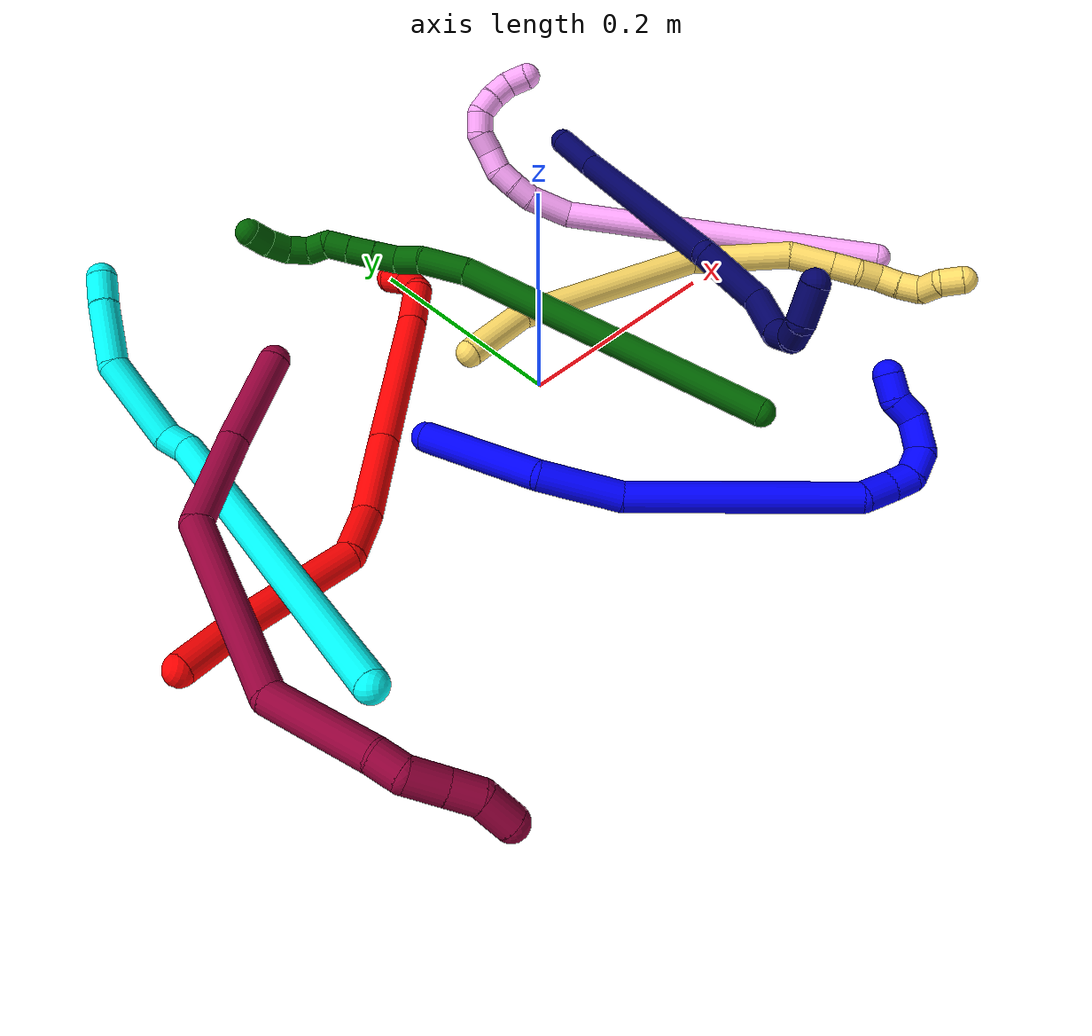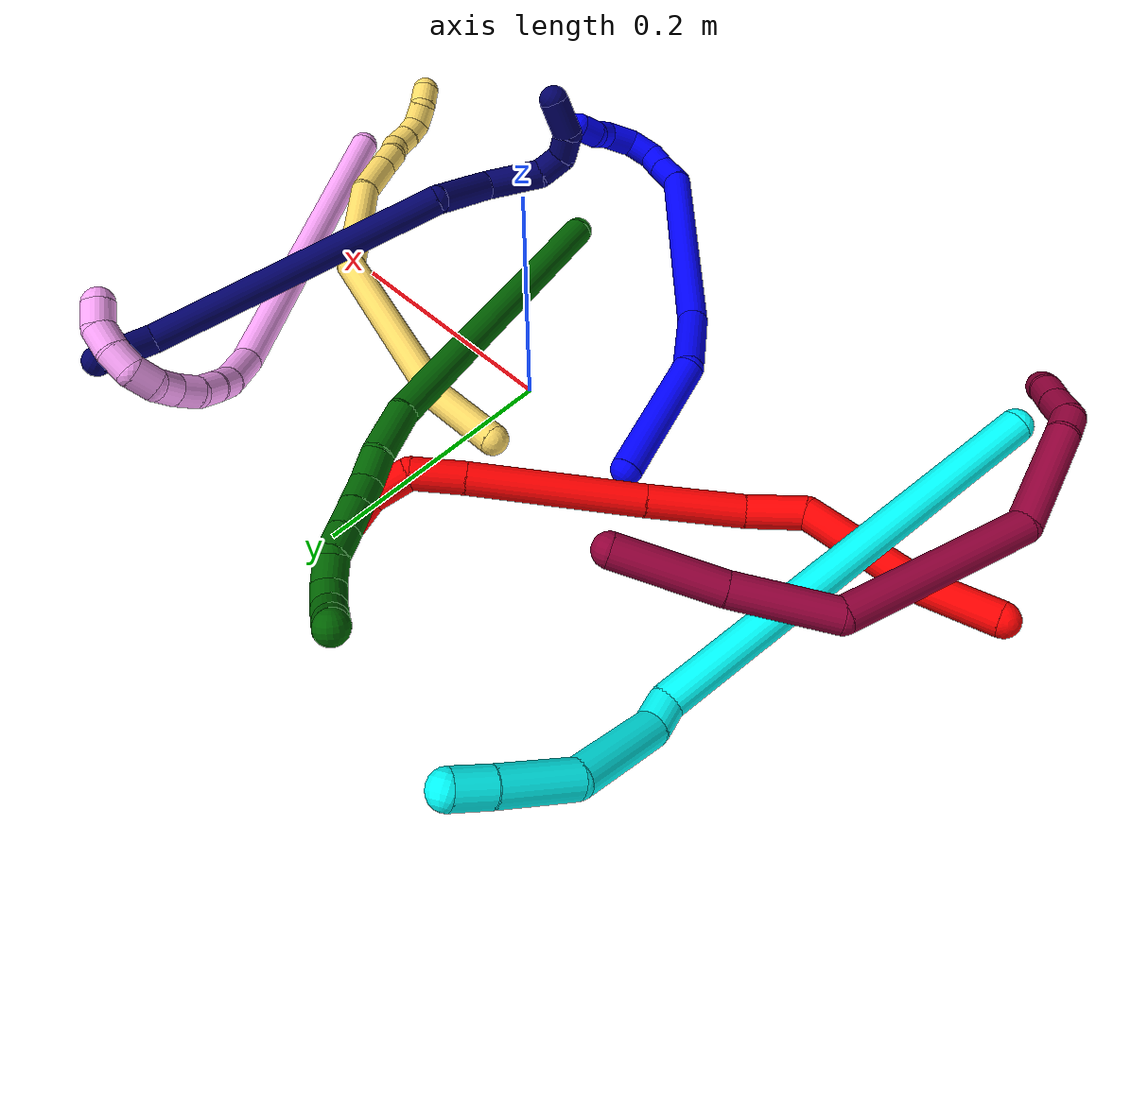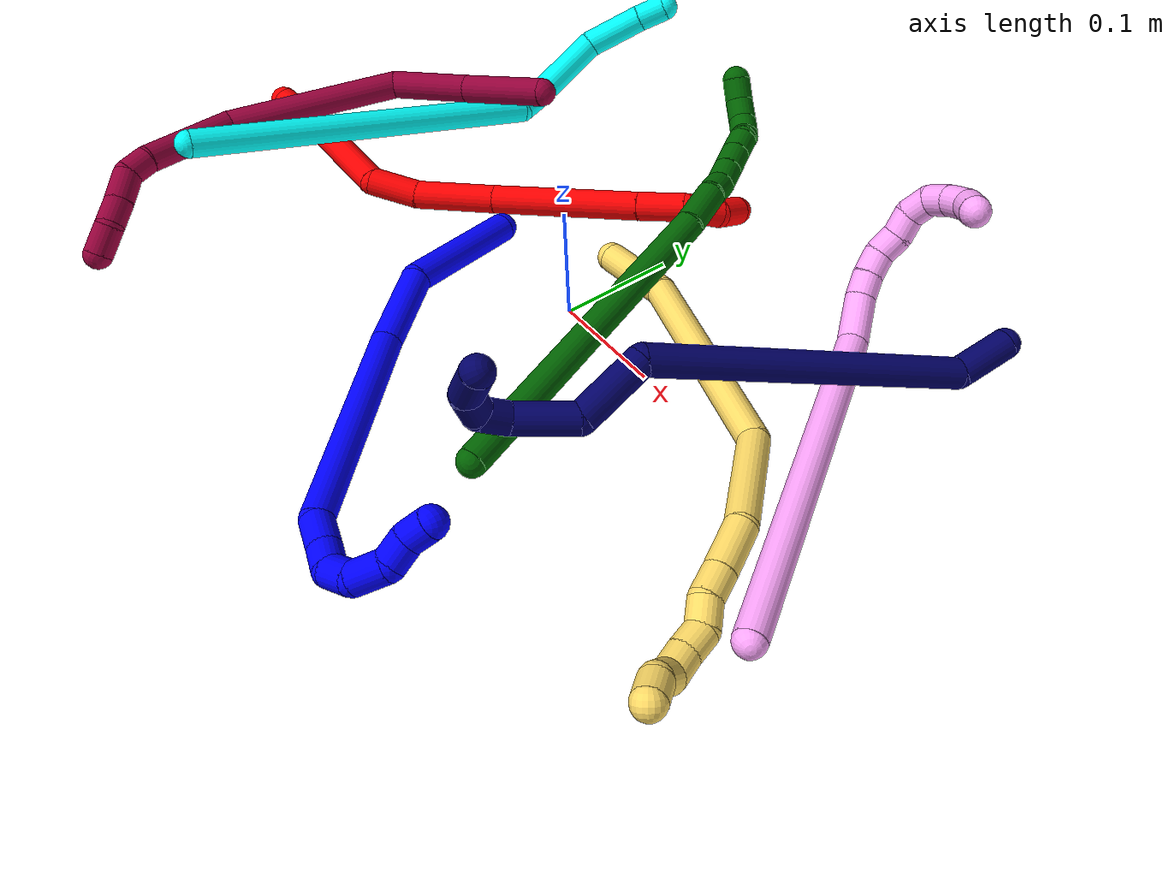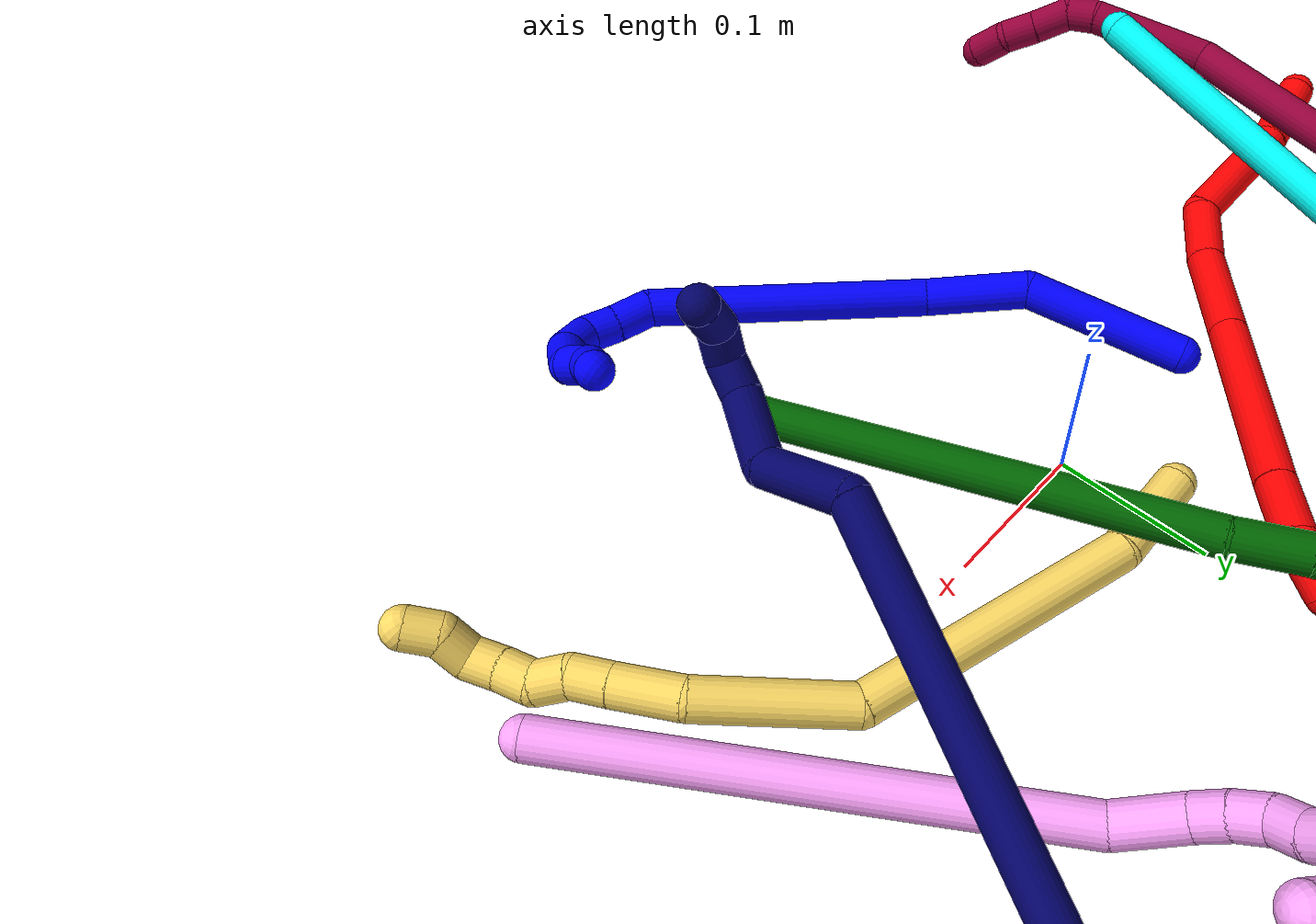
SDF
<sdf version="1.7">
 <world name="default">
  <plugin name="TubeGeneratorPlugin" filename="libtube_generator_plugin.so"/>
  <model name="photoneo_s_sensor">
   <static>1</static>
   <pose>0 0 2 1.57079 1.57079 3.14159</pose>
   <link name="link">
    <inertial><mass>0.1</mass></inertial>
    <sensor name="sensor" type="depth">
     <update_rate>30</update_rate>
     <camera>
      <horizontal_fov>1.22</horizontal_fov>
      <image><width>1920</width><height>1200</height><format>B8G8R8</format></image>
      <clip><near>0.1</near><far>4</far></clip>
      <depth_camera><output>points</output></depth_camera>
     </camera>
     <plugin name="camera_plugin" filename="libgazebo_ros_depth_camera.so">
      <baseline>0.2</baseline>
      <alwaysOn>1</alwaysOn>
      <updateRate>0.0</updateRate>
      <cameraName>camera_ir</cameraName>
      <imageTopicName>/camera/color/image_raw</imageTopicName>
      <cameraInfoTopicName>/camera/color/camera_info</cameraInfoTopicName>
      <depthImageTopicName>/camera/depth/image_raw</depthImageTopicName>
      <depthImageCameraInfoTopicName>/camera/depth/camera_info</depthImageCameraInfoTopicName>
      <pointCloudTopicName>/camera/depth/points</pointCloudTopicName>
      <frameName>fr_optical</frameName>
      <pointCloudCutoff>0.1</pointCloudCutoff>
      <pointCloudCutoffMax>2.0</pointCloudCutoffMax>
      <distortionK1>0</distortionK1>
      <distortionK2>0</distortionK2>
      <distortionK3>0</distortionK3>
      <distortionT1>0</distortionT1>
      <distortionT2>0</distortionT2>
      <CxPrime>0</CxPrime>
      <Cx>0</Cx>
      <Cy>0</Cy>
      <focalLength>0</focalLength>
      <hackBaseline>0</hackBaseline>
     </plugin>
    </sensor>
   </link>
  </model>
  <gravity>0 0 -9.8</gravity>
  <magnetic_field>6e-06 2.3e-05 -4.2e-05</magnetic_field>
  <atmosphere type="adiabatic"/>
  <physics name="default_physics" default="0" type="ode">
   <max_step_size>0.003</max_step_size>
   <real_time_factor>1</real_time_factor>
   <real_time_update_rate>1000</real_time_update_rate>
   <max_contacts>10000</max_contacts>
   <ode>
    <solver>
     <type>quick</type>
     <iters>100</iters>
     <sor>1.3</sor>
     <use_dynamic_moi_rescaling>0</use_dynamic_moi_rescaling>
    </solver>
    <constraints>
     <contact_max_correcting_vel>0</contact_max_correcting_vel>
     <contact_surface_layer>0.001</contact_surface_layer>
     <cfm>0</cfm>
     <erp>0.2</erp>
    </constraints>
   </ode>
  </physics>
  <scene><ambient>0.4 0.4 0.4 1</ambient><background>0.7 0.7 0.7 1</background><shadows>0</shadows></scene>
  <audio><device>default</device></audio>
  <spherical_coordinates>
   <surface_model>EARTH_WGS84</surface_model>
   <latitude_deg>0</latitude_deg>
   <longitude_deg>0</longitude_deg>
   <elevation>0</elevation>
   <heading_deg>0</heading_deg>
  </spherical_coordinates>
  <model name="bin">
   <static>1</static>
   <link name="bottom">
    <collision name="collision-bottom">
     <pose>0 0 -0.01 0 -0 0</pose>
     <geometry><box><size>0.8 0.6 0.02</size></box></geometry>
     <surface>
      <friction><ode><mu>100</mu><mu2>100</mu2></ode></friction>
      <contact><collide_bitmask>65535</collide_bitmask></contact>
     </surface>
    </collision>
   </link>
   <link name="west_wall">
    <collision name="collision-west_wall">
     <pose>-0.41 0 0.1 0 -0 0</pose>
     <geometry><box><size>0.02 0.6 0.2</size></box></geometry>
     <surface>
      <friction><ode><mu>100</mu><mu2>100</mu2></ode></friction>
      <contact><collide_bitmask>65535</collide_bitmask></contact>
     </surface>
    </collision>
   </link>
   <link name="east_wall">
    <collision name="collision-east_wall">
     <pose>0.41 0 0.1 0 -0 0</pose>
     <geometry><box><size>0.02 0.6 0.2</size></box></geometry>
     <surface>
      <friction><ode><mu>100</mu><mu2>100</mu2></ode></friction>
      <contact><collide_bitmask>65535</collide_bitmask></contact>
     </surface>
    </collision>
   </link>
   <link name="south_wall">
    <collision name="collision-south_wall">
     <pose>0 -0.31 0.1 0 -0 0</pose>
     <geometry><box><size>0.8 0.02 0.2</size></box></geometry>
     <surface>
      <friction><ode><mu>100</mu><mu2>100</mu2></ode></friction>
      <contact><collide_bitmask>65535</collide_bitmask></contact>
     </surface>
    </collision>
   </link>
   <link name="north_wall">
    <collision name="collision-north_wall">
     <pose>0 0.31 0.1 0 -0 0</pose>
     <geometry><box><size>0.8 0.02 0.2</size></box></geometry>
     <surface>
      <friction><ode><mu>100</mu><mu2>100</mu2></ode></friction>
      <contact><collide_bitmask>65535</collide_bitmask></contact>
     </surface>
    </collision>
   </link>
  </model>
  <model name="1">
   <static>0</static>
   <link name="1">
    <collision name="collision-cylinder-e_1_1_4">
     <pose>0.000866 -0.011424 0.051943 0.216487 0.016278 0.001769</pose>
     <geometry><cylinder><radius>0.0125</radius><length>0.106382</length></cylinder></geometry>
     <surface>
      <friction><ode><mu>1.16</mu><mu2>1.16</mu2><slip1>0</slip1><slip2>0</slip2></ode></friction>
      <contact><ode><kp>1e+06</kp><kd>1</kd><max_vel>0</max_vel><min_depth>0.001</min_depth></ode></contact>
     </surface>
    </collision>
    <visual name="visual-cylinder-e_1_1_4">
     <pose>0.000866 -0.011424 0.051943 0.216487 0.016278 0.001769</pose>
     <geometry><cylinder><radius>0.0125</radius><length>0.106382</length></cylinder></geometry>
     <material><ambient>0 0 1 1</ambient></material>
    </visual>
    <collision name="collision-cylinder-e_2_4_5">
     <pose>0.008972 -0.043232 0.13002 0.662408 0.215082 0.074213</pose>
     <geometry><cylinder><radius>0.0125</radius><length>0.067851</length></cylinder></geometry>
     <surface>
      <friction><ode><mu>1.16</mu><mu2>1.16</mu2><slip1>0</slip1><slip2>0</slip2></ode></friction>
      <contact><ode><kp>1e+06</kp><kd>1</kd><max_vel>0</max_vel><min_depth>0.001</min_depth></ode></contact>
     </surface>
    </collision>
    <visual name="visual-cylinder-e_2_4_5">
     <pose>0.008972 -0.043232 0.13002 0.662408 0.215082 0.074213</pose>
     <geometry><cylinder><radius>0.0125</radius><length>0.067851</length></cylinder></geometry>
     <material><ambient>0 0 1 1</ambient></material>
    </visual>
    <collision name="collision-cylinder-e_3_5_6">
     <pose>0.055796 -0.107141 0.227901 0.545298 0.440752 0.125111</pose>
     <geometry><cylinder><radius>0.0125</radius><length>0.185568</length></cylinder></geometry>
     <surface>
      <friction><ode><mu>1.16</mu><mu2>1.16</mu2><slip1>0</slip1><slip2>0</slip2></ode></friction>
      <contact><ode><kp>1e+06</kp><kd>1</kd><max_vel>0</max_vel><min_depth>0.001</min_depth></ode></contact>
     </surface>
    </collision>
    <visual name="visual-cylinder-e_3_5_6">
     <pose>0.055796 -0.107141 0.227901 0.545298 0.440752 0.125111</pose>
     <geometry><cylinder><radius>0.0125</radius><length>0.185568</length></cylinder></geometry>
     <material><ambient>0 0 1 1</ambient></material>
    </visual>
    <collision name="collision-cylinder-e_4_6_7">
     <pose>0.104959 -0.157859 0.304806 0.948635 0.824871 0.441929</pose>
     <geometry><cylinder><radius>0.0125</radius><length>0.026084</length></cylinder></geometry>
     <surface>
      <friction><ode><mu>1.16</mu><mu2>1.16</mu2><slip1>0</slip1><slip2>0</slip2></ode></friction>
      <contact><ode><kp>1e+06</kp><kd>1</kd><max_vel>0</max_vel><min_depth>0.001</min_depth></ode></contact>
     </surface>
    </collision>
    <visual name="visual-cylinder-e_4_6_7">
     <pose>0.104959 -0.157859 0.304806 0.948635 0.824871 0.441929</pose>
     <geometry><cylinder><radius>0.0125</radius><length>0.026084</length></cylinder></geometry>
     <material><ambient>0 0 1 1</ambient></material>
    </visual>
    <collision name="collision-cylinder-e_5_7_8">
     <pose>0.122565 -0.169888 0.314643 0.801987 0.873131 0.390594</pose>
     <geometry><cylinder><radius>0.0125</radius><length>0.02095</length></cylinder></geometry>
     <surface>
      <friction><ode><mu>1.16</mu><mu2>1.16</mu2><slip1>0</slip1><slip2>0</slip2></ode></friction>
      <contact><ode><kp>1e+06</kp><kd>1</kd><max_vel>0</max_vel><min_depth>0.001</min_depth></ode></contact>
     </surface>
    </collision>
    <visual name="visual-cylinder-e_5_7_8">
     <pose>0.122565 -0.169888 0.314643 0.801987 0.873131 0.390594</pose>
     <geometry><cylinder><radius>0.0125</radius><length>0.02095</length></cylinder></geometry>
     <material><ambient>0 0 1 1</ambient></material>
    </visual>
    <collision name="collision-cylinder-e_6_8_9">
     <pose>0.142382 -0.175844 0.319013 1.83995 1.47269 1.74412</pose>
     <geometry><cylinder><radius>0.0125</radius><length>0.023692</length></cylinder></geometry>
     <surface>
      <friction><ode><mu>1.16</mu><mu2>1.16</mu2><slip1>0</slip1><slip2>0</slip2></ode></friction>
      <contact><ode><kp>1e+06</kp><kd>1</kd><max_vel>0</max_vel><min_depth>0.001</min_depth></ode></contact>
     </surface>
    </collision>
    <visual name="visual-cylinder-e_6_8_9">
     <pose>0.142382 -0.175844 0.319013 1.83995 1.47269 1.74412</pose>
     <geometry><cylinder><radius>0.0125</radius><length>0.023692</length></cylinder></geometry>
     <material><ambient>0 0 1 1</ambient></material>
    </visual>
    <collision name="collision-cylinder-e_7_9_10">
     <pose>0.165902 -0.17274 0.312024 -2.57799 0.977946 -2.14497</pose>
     <geometry><cylinder><radius>0.0125</radius><length>0.02829</length></cylinder></geometry>
     <surface>
      <friction><ode><mu>1.16</mu><mu2>1.16</mu2><slip1>0</slip1><slip2>0</slip2></ode></friction>
      <contact><ode><kp>1e+06</kp><kd>1</kd><max_vel>0</max_vel><min_depth>0.001</min_depth></ode></contact>
     </surface>
    </collision>
    <visual name="visual-cylinder-e_7_9_10">
     <pose>0.165902 -0.17274 0.312024 -2.57799 0.977946 -2.14497</pose>
     <geometry><cylinder><radius>0.0125</radius><length>0.02829</length></cylinder></geometry>
     <material><ambient>0 0 1 1</ambient></material>
    </visual>
    <collision name="collision-cylinder-e_8_10_11">
     <pose>0.18096 -0.161588 0.29871 -2.33432 0.333851 -0.751546</pose>
     <geometry><cylinder><radius>0.0125</radius><length>0.020306</length></cylinder></geometry>
     <surface>
      <friction><ode><mu>1.16</mu><mu2>1.16</mu2><slip1>0</slip1><slip2>0</slip2></ode></friction>
      <contact><ode><kp>1e+06</kp><kd>1</kd><max_vel>0</max_vel><min_depth>0.001</min_depth></ode></contact>
     </surface>
    </collision>
    <visual name="visual-cylinder-e_8_10_11">
     <pose>0.18096 -0.161588 0.29871 -2.33432 0.333851 -0.751546</pose>
     <geometry><cylinder><radius>0.0125</radius><length>0.020306</length></cylinder></geometry>
     <material><ambient>0 0 1 1</ambient></material>
    </visual>
    <collision name="collision-cylinder-e_9_11_2">
     <pose>0.192224 -0.149579 0.287587 -2.29465 0.863889 -1.59325</pose>
     <geometry><cylinder><radius>0.0125</radius><length>0.020876</length></cylinder></geometry>
     <surface>
      <friction><ode><mu>1.16</mu><mu2>1.16</mu2><slip1>0</slip1><slip2>0</slip2></ode></friction>
      <contact><ode><kp>1e+06</kp><kd>1</kd><max_vel>0</max_vel><min_depth>0.001</min_depth></ode></contact>
     </surface>
    </collision>
    <visual name="visual-cylinder-e_9_11_2">
     <pose>0.192224 -0.149579 0.287587 -2.29465 0.863889 -1.59325</pose>
     <geometry><cylinder><radius>0.0125</radius><length>0.020876</length></cylinder></geometry>
     <material><ambient>0 0 1 1</ambient></material>
    </visual>
    <collision name="collision-sphere-2">
     <pose>0.200161 -0.144499 0.283097 0 -0 0</pose>
     <geometry><sphere><radius>0.0125</radius></sphere></geometry>
     <surface>
      <friction><ode><mu>1.16</mu><mu2>1.16</mu2><slip1>0</slip1><slip2>0</slip2></ode></friction>
      <contact><ode><kp>1e+06</kp><kd>1</kd><max_vel>0</max_vel><min_depth>0.001</min_depth></ode></contact>
     </surface>
    </collision>
    <visual name="visual-sphere-2">
     <pose>0.200161 -0.144499 0.283097 0 -0 0</pose>
     <geometry><sphere><radius>0.0125</radius></sphere></geometry>
     <material><ambient>0 0 1 1</ambient></material>
    </visual>
    <collision name="collision-sphere-11">
     <pose>0.184287 -0.154658 0.292077 0 -0 0</pose>
     <geometry><sphere><radius>0.0125</radius></sphere></geometry>
     <surface>
      <friction><ode><mu>1.16</mu><mu2>1.16</mu2><slip1>0</slip1><slip2>0</slip2></ode></friction>
      <contact><ode><kp>1e+06</kp><kd>1</kd><max_vel>0</max_vel><min_depth>0.001</min_depth></ode></contact>
     </surface>
    </collision>
    <visual name="visual-sphere-11">
     <pose>0.184287 -0.154658 0.292077 0 -0 0</pose>
     <geometry><sphere><radius>0.0125</radius></sphere></geometry>
     <material><ambient>0 0 1 1</ambient></material>
    </visual>
    <collision name="collision-sphere-10">
     <pose>0.177633 -0.168518 0.305343 0 -0 0</pose>
     <geometry><sphere><radius>0.0125</radius></sphere></geometry>
     <surface>
      <friction><ode><mu>1.16</mu><mu2>1.16</mu2><slip1>0</slip1><slip2>0</slip2></ode></friction>
      <contact><ode><kp>1e+06</kp><kd>1</kd><max_vel>0</max_vel><min_depth>0.001</min_depth></ode></contact>
     </surface>
    </collision>
    <visual name="visual-sphere-10">
     <pose>0.177633 -0.168518 0.305343 0 -0 0</pose>
     <geometry><sphere><radius>0.0125</radius></sphere></geometry>
     <material><ambient>0 0 1 1</ambient></material>
    </visual>
    <collision name="collision-sphere-9">
     <pose>0.154171 -0.176962 0.318705 0 -0 0</pose>
     <geometry><sphere><radius>0.0125</radius></sphere></geometry>
     <surface>
      <friction><ode><mu>1.16</mu><mu2>1.16</mu2><slip1>0</slip1><slip2>0</slip2></ode></friction>
      <contact><ode><kp>1e+06</kp><kd>1</kd><max_vel>0</max_vel><min_depth>0.001</min_depth></ode></contact>
     </surface>
    </collision>
    <visual name="visual-sphere-9">
     <pose>0.154171 -0.176962 0.318705 0 -0 0</pose>
     <geometry><sphere><radius>0.0125</radius></sphere></geometry>
     <material><ambient>0 0 1 1</ambient></material>
    </visual>
    <collision name="collision-sphere-4">
     <pose>0.001732 -0.022848 0.103885 0 -0 0</pose>
     <geometry><sphere><radius>0.0125</radius></sphere></geometry>
     <surface>
      <friction><ode><mu>1.16</mu><mu2>1.16</mu2><slip1>0</slip1><slip2>0</slip2></ode></friction>
      <contact><ode><kp>1e+06</kp><kd>1</kd><max_vel>0</max_vel><min_depth>0.001</min_depth></ode></contact>
     </surface>
    </collision>
    <visual name="visual-sphere-4">
     <pose>0.001732 -0.022848 0.103885 0 -0 0</pose>
     <geometry><sphere><radius>0.0125</radius></sphere></geometry>
     <material><ambient>0 0 1 1</ambient></material>
    </visual>
    <collision name="collision-sphere-1">
     <geometry><sphere><radius>0.0125</radius></sphere></geometry>
     <surface>
      <friction><ode><mu>1.16</mu><mu2>1.16</mu2><slip1>0</slip1><slip2>0</slip2></ode></friction>
      <contact><ode><kp>1e+06</kp><kd>1</kd><max_vel>0</max_vel><min_depth>0.001</min_depth></ode></contact>
     </surface>
    </collision>
    <visual name="visual-sphere-1">
     <geometry><sphere><radius>0.0125</radius></sphere></geometry>
     <material><ambient>0 0 1 1</ambient></material>
    </visual>
    <collision name="collision-sphere-8">
     <pose>0.130593 -0.174725 0.319322 0 -0 0</pose>
     <geometry><sphere><radius>0.0125</radius></sphere></geometry>
     <surface>
      <friction><ode><mu>1.16</mu><mu2>1.16</mu2><slip1>0</slip1><slip2>0</slip2></ode></friction>
      <contact><ode><kp>1e+06</kp><kd>1</kd><max_vel>0</max_vel><min_depth>0.001</min_depth></ode></contact>
     </surface>
    </collision>
    <visual name="visual-sphere-8">
     <pose>0.130593 -0.174725 0.319322 0 -0 0</pose>
     <geometry><sphere><radius>0.0125</radius></sphere></geometry>
     <material><ambient>0 0 1 1</ambient></material>
    </visual>
    <collision name="collision-sphere-5">
     <pose>0.016213 -0.063616 0.156154 0 -0 0</pose>
     <geometry><sphere><radius>0.0125</radius></sphere></geometry>
     <surface>
      <friction><ode><mu>1.16</mu><mu2>1.16</mu2><slip1>0</slip1><slip2>0</slip2></ode></friction>
      <contact><ode><kp>1e+06</kp><kd>1</kd><max_vel>0</max_vel><min_depth>0.001</min_depth></ode></contact>
     </surface>
    </collision>
    <visual name="visual-sphere-5">
     <pose>0.016213 -0.063616 0.156154 0 -0 0</pose>
     <geometry><sphere><radius>0.0125</radius></sphere></geometry>
     <material><ambient>0 0 1 1</ambient></material>
    </visual>
    <collision name="collision-sphere-6">
     <pose>0.09538 -0.150667 0.299647 0 -0 0</pose>
     <geometry><sphere><radius>0.0125</radius></sphere></geometry>
     <surface>
      <friction><ode><mu>1.16</mu><mu2>1.16</mu2><slip1>0</slip1><slip2>0</slip2></ode></friction>
      <contact><ode><kp>1e+06</kp><kd>1</kd><max_vel>0</max_vel><min_depth>0.001</min_depth></ode></contact>
     </surface>
    </collision>
    <visual name="visual-sphere-6">
     <pose>0.09538 -0.150667 0.299647 0 -0 0</pose>
     <geometry><sphere><radius>0.0125</radius></sphere></geometry>
     <material><ambient>0 0 1 1</ambient></material>
    </visual>
    <collision name="collision-sphere-7">
     <pose>0.114538 -0.165052 0.309964 0 -0 0</pose>
     <geometry><sphere><radius>0.0125</radius></sphere></geometry>
     <surface>
      <friction><ode><mu>1.16</mu><mu2>1.16</mu2><slip1>0</slip1><slip2>0</slip2></ode></friction>
      <contact><ode><kp>1e+06</kp><kd>1</kd><max_vel>0</max_vel><min_depth>0.001</min_depth></ode></contact>
     </surface>
    </collision>
    <visual name="visual-sphere-7">
     <pose>0.114538 -0.165052 0.309964 0 -0 0</pose>
     <geometry><sphere><radius>0.0125</radius></sphere></geometry>
     <material><ambient>0 0 1 1</ambient></material>
    </visual>
    <inertial>
     <pose>0.064229 -0.094328 0.199272 0 -0 0</pose>
     <mass>0.5</mass>
     <inertia>
      <ixx>0.000696</ixx>
      <ixy>0</ixy>
      <ixz>0</ixz>
      <iyy>0.000656</iyy>
      <iyz>0</iyz>
      <izz>6.7e-05</izz>
     </inertia>
    </inertial>
   </link>
   <pose>-0.116416 0.011802 0.011763 1.22975 -0.429821 0.303372</pose>
  </model>
  <model name="2">
   <static>0</static>
   <link name="2">
    <collision name="collision-cylinder-e_1_1_4">
     <pose>0.001031 0.019089 0.019875 -0.76524 0.037411 -0.015058</pose>
     <geometry><cylinder><radius>0.0125</radius><length>0.055154</length></cylinder></geometry>
     <surface>
      <friction><ode><mu>1.16</mu><mu2>1.16</mu2><slip1>0</slip1><slip2>0</slip2></ode></friction>
      <contact><ode><kp>1e+06</kp><kd>1</kd><max_vel>0</max_vel><min_depth>0.001</min_depth></ode></contact>
     </surface>
    </collision>
    <visual name="visual-cylinder-e_1_1_4">
     <pose>0.001031 0.019089 0.019875 -0.76524 0.037411 -0.015058</pose>
     <geometry><cylinder><radius>0.0125</radius><length>0.055154</length></cylinder></geometry>
     <material><ambient>1 0 0 1</ambient></material>
    </visual>
    <collision name="collision-cylinder-e_2_4_5">
     <pose>-0.005226 0.069563 0.074713 -0.731512 -0.15391 0.059045</pose>
     <geometry><cylinder><radius>0.0125</radius><length>0.095091</length></cylinder></geometry>
     <surface>
      <friction><ode><mu>1.16</mu><mu2>1.16</mu2><slip1>0</slip1><slip2>0</slip2></ode></friction>
      <contact><ode><kp>1e+06</kp><kd>1</kd><max_vel>0</max_vel><min_depth>0.001</min_depth></ode></contact>
     </surface>
    </collision>
    <visual name="visual-cylinder-e_2_4_5">
     <pose>-0.005226 0.069563 0.074713 -0.731512 -0.15391 0.059045</pose>
     <geometry><cylinder><radius>0.0125</radius><length>0.095091</length></cylinder></geometry>
     <material><ambient>1 0 0 1</ambient></material>
    </visual>
    <collision name="collision-cylinder-e_3_5_6">
     <pose>-0.004186 0.119019 0.119549 -1.07079 0.38436 -0.229829</pose>
     <geometry><cylinder><radius>0.0125</radius><length>0.044426</length></cylinder></geometry>
     <surface>
      <friction><ode><mu>1.16</mu><mu2>1.16</mu2><slip1>0</slip1><slip2>0</slip2></ode></friction>
      <contact><ode><kp>1e+06</kp><kd>1</kd><max_vel>0</max_vel><min_depth>0.001</min_depth></ode></contact>
     </surface>
    </collision>
    <visual name="visual-cylinder-e_3_5_6">
     <pose>-0.004186 0.119019 0.119549 -1.07079 0.38436 -0.229829</pose>
     <geometry><cylinder><radius>0.0125</radius><length>0.044426</length></cylinder></geometry>
     <material><ambient>1 0 0 1</ambient></material>
    </visual>
    <collision name="collision-cylinder-e_4_6_7">
     <pose>0.014742 0.170812 0.138863 -1.29781 0.293899 -0.223597</pose>
     <geometry><cylinder><radius>0.0125</radius><length>0.073174</length></cylinder></geometry>
     <surface>
      <friction><ode><mu>1.16</mu><mu2>1.16</mu2><slip1>0</slip1><slip2>0</slip2></ode></friction>
      <contact><ode><kp>1e+06</kp><kd>1</kd><max_vel>0</max_vel><min_depth>0.001</min_depth></ode></contact>
     </surface>
    </collision>
    <visual name="visual-cylinder-e_4_6_7">
     <pose>0.014742 0.170812 0.138863 -1.29781 0.293899 -0.223597</pose>
     <geometry><cylinder><radius>0.0125</radius><length>0.073174</length></cylinder></geometry>
     <material><ambient>1 0 0 1</ambient></material>
    </visual>
    <collision name="collision-cylinder-e_5_7_8">
     <pose>0.04312 0.265628 0.164801 -1.30707 0.273887 -0.210285</pose>
     <geometry><cylinder><radius>0.0125</radius><length>0.131466</length></cylinder></geometry>
     <surface>
      <friction><ode><mu>1.16</mu><mu2>1.16</mu2><slip1>0</slip1><slip2>0</slip2></ode></friction>
      <contact><ode><kp>1e+06</kp><kd>1</kd><max_vel>0</max_vel><min_depth>0.001</min_depth></ode></contact>
     </surface>
    </collision>
    <visual name="visual-cylinder-e_5_7_8">
     <pose>0.04312 0.265628 0.164801 -1.30707 0.273887 -0.210285</pose>
     <geometry><cylinder><radius>0.0125</radius><length>0.131466</length></cylinder></geometry>
     <material><ambient>1 0 0 1</ambient></material>
    </visual>
    <collision name="collision-cylinder-e_6_8_9">
     <pose>0.0672 0.345968 0.186032 -1.32958 0.307803 -0.241994</pose>
     <geometry><cylinder><radius>0.0125</radius><length>0.041592</length></cylinder></geometry>
     <surface>
      <friction><ode><mu>1.16</mu><mu2>1.16</mu2><slip1>0</slip1><slip2>0</slip2></ode></friction>
      <contact><ode><kp>1e+06</kp><kd>1</kd><max_vel>0</max_vel><min_depth>0.001</min_depth></ode></contact>
     </surface>
    </collision>
    <visual name="visual-cylinder-e_6_8_9">
     <pose>0.0672 0.345968 0.186032 -1.32958 0.307803 -0.241994</pose>
     <geometry><cylinder><radius>0.0125</radius><length>0.041592</length></cylinder></geometry>
     <material><ambient>1 0 0 1</ambient></material>
    </visual>
    <collision name="collision-cylinder-e_7_9_10">
     <pose>0.087046 0.374533 0.193968 -1.23982 0.941849 -0.69713</pose>
     <geometry><cylinder><radius>0.0125</radius><length>0.033503</length></cylinder></geometry>
     <surface>
      <friction><ode><mu>1.16</mu><mu2>1.16</mu2><slip1>0</slip1><slip2>0</slip2></ode></friction>
      <contact><ode><kp>1e+06</kp><kd>1</kd><max_vel>0</max_vel><min_depth>0.001</min_depth></ode></contact>
     </surface>
    </collision>
    <visual name="visual-cylinder-e_7_9_10">
     <pose>0.087046 0.374533 0.193968 -1.23982 0.941849 -0.69713</pose>
     <geometry><cylinder><radius>0.0125</radius><length>0.033503</length></cylinder></geometry>
     <material><ambient>1 0 0 1</ambient></material>
    </visual>
    <collision name="collision-cylinder-e_8_10_2">
     <pose>0.112743 0.387376 0.195241 -2.07199 1.2515 -1.76823</pose>
     <geometry><cylinder><radius>0.0125</radius><length>0.025595</length></cylinder></geometry>
     <surface>
      <friction><ode><mu>1.16</mu><mu2>1.16</mu2><slip1>0</slip1><slip2>0</slip2></ode></friction>
      <contact><ode><kp>1e+06</kp><kd>1</kd><max_vel>0</max_vel><min_depth>0.001</min_depth></ode></contact>
     </surface>
    </collision>
    <visual name="visual-cylinder-e_8_10_2">
     <pose>0.112743 0.387376 0.195241 -2.07199 1.2515 -1.76823</pose>
     <geometry><cylinder><radius>0.0125</radius><length>0.025595</length></cylinder></geometry>
     <material><ambient>1 0 0 1</ambient></material>
    </visual>
    <collision name="collision-sphere-2">
     <pose>0.124893 0.390899 0.193311 0 -0 0</pose>
     <geometry><sphere><radius>0.0125</radius></sphere></geometry>
     <surface>
      <friction><ode><mu>1.16</mu><mu2>1.16</mu2><slip1>0</slip1><slip2>0</slip2></ode></friction>
      <contact><ode><kp>1e+06</kp><kd>1</kd><max_vel>0</max_vel><min_depth>0.001</min_depth></ode></contact>
     </surface>
    </collision>
    <visual name="visual-sphere-2">
     <pose>0.124893 0.390899 0.193311 0 -0 0</pose>
     <geometry><sphere><radius>0.0125</radius></sphere></geometry>
     <material><ambient>1 0 0 1</ambient></material>
    </visual>
    <collision name="collision-sphere-10">
     <pose>0.100592 0.383853 0.197171 0 -0 0</pose>
     <geometry><sphere><radius>0.0125</radius></sphere></geometry>
     <surface>
      <friction><ode><mu>1.16</mu><mu2>1.16</mu2><slip1>0</slip1><slip2>0</slip2></ode></friction>
      <contact><ode><kp>1e+06</kp><kd>1</kd><max_vel>0</max_vel><min_depth>0.001</min_depth></ode></contact>
     </surface>
    </collision>
    <visual name="visual-sphere-10">
     <pose>0.100592 0.383853 0.197171 0 -0 0</pose>
     <geometry><sphere><radius>0.0125</radius></sphere></geometry>
     <material><ambient>1 0 0 1</ambient></material>
    </visual>
    <collision name="collision-sphere-9">
     <pose>0.0735 0.365213 0.190766 0 -0 0</pose>
     <geometry><sphere><radius>0.0125</radius></sphere></geometry>
     <surface>
      <friction><ode><mu>1.16</mu><mu2>1.16</mu2><slip1>0</slip1><slip2>0</slip2></ode></friction>
      <contact><ode><kp>1e+06</kp><kd>1</kd><max_vel>0</max_vel><min_depth>0.001</min_depth></ode></contact>
     </surface>
    </collision>
    <visual name="visual-sphere-9">
     <pose>0.0735 0.365213 0.190766 0 -0 0</pose>
     <geometry><sphere><radius>0.0125</radius></sphere></geometry>
     <material><ambient>1 0 0 1</ambient></material>
    </visual>
    <collision name="collision-sphere-4">
     <pose>0.002063 0.038179 0.03975 0 -0 0</pose>
     <geometry><sphere><radius>0.0125</radius></sphere></geometry>
     <surface>
      <friction><ode><mu>1.16</mu><mu2>1.16</mu2><slip1>0</slip1><slip2>0</slip2></ode></friction>
      <contact><ode><kp>1e+06</kp><kd>1</kd><max_vel>0</max_vel><min_depth>0.001</min_depth></ode></contact>
     </surface>
    </collision>
    <visual name="visual-sphere-4">
     <pose>0.002063 0.038179 0.03975 0 -0 0</pose>
     <geometry><sphere><radius>0.0125</radius></sphere></geometry>
     <material><ambient>1 0 0 1</ambient></material>
    </visual>
    <collision name="collision-sphere-1">
     <geometry><sphere><radius>0.0125</radius></sphere></geometry>
     <surface>
      <friction><ode><mu>1.16</mu><mu2>1.16</mu2><slip1>0</slip1><slip2>0</slip2></ode></friction>
      <contact><ode><kp>1e+06</kp><kd>1</kd><max_vel>0</max_vel><min_depth>0.001</min_depth></ode></contact>
     </surface>
    </collision>
    <visual name="visual-sphere-1">
     <geometry><sphere><radius>0.0125</radius></sphere></geometry>
     <material><ambient>1 0 0 1</ambient></material>
    </visual>
    <collision name="collision-sphere-8">
     <pose>0.060899 0.326723 0.181297 0 -0 0</pose>
     <geometry><sphere><radius>0.0125</radius></sphere></geometry>
     <surface>
      <friction><ode><mu>1.16</mu><mu2>1.16</mu2><slip1>0</slip1><slip2>0</slip2></ode></friction>
      <contact><ode><kp>1e+06</kp><kd>1</kd><max_vel>0</max_vel><min_depth>0.001</min_depth></ode></contact>
     </surface>
    </collision>
    <visual name="visual-sphere-8">
     <pose>0.060899 0.326723 0.181297 0 -0 0</pose>
     <geometry><sphere><radius>0.0125</radius></sphere></geometry>
     <material><ambient>1 0 0 1</ambient></material>
    </visual>
    <collision name="collision-sphere-5">
     <pose>-0.012515 0.100948 0.109677 0 -0 0</pose>
     <geometry><sphere><radius>0.0125</radius></sphere></geometry>
     <surface>
      <friction><ode><mu>1.16</mu><mu2>1.16</mu2><slip1>0</slip1><slip2>0</slip2></ode></friction>
      <contact><ode><kp>1e+06</kp><kd>1</kd><max_vel>0</max_vel><min_depth>0.001</min_depth></ode></contact>
     </surface>
    </collision>
    <visual name="visual-sphere-5">
     <pose>-0.012515 0.100948 0.109677 0 -0 0</pose>
     <geometry><sphere><radius>0.0125</radius></sphere></geometry>
     <material><ambient>1 0 0 1</ambient></material>
    </visual>
    <collision name="collision-sphere-6">
     <pose>0.004143 0.13709 0.129422 0 -0 0</pose>
     <geometry><sphere><radius>0.0125</radius></sphere></geometry>
     <surface>
      <friction><ode><mu>1.16</mu><mu2>1.16</mu2><slip1>0</slip1><slip2>0</slip2></ode></friction>
      <contact><ode><kp>1e+06</kp><kd>1</kd><max_vel>0</max_vel><min_depth>0.001</min_depth></ode></contact>
     </surface>
    </collision>
    <visual name="visual-sphere-6">
     <pose>0.004143 0.13709 0.129422 0 -0 0</pose>
     <geometry><sphere><radius>0.0125</radius></sphere></geometry>
     <material><ambient>1 0 0 1</ambient></material>
    </visual>
    <collision name="collision-sphere-7">
     <pose>0.025341 0.204533 0.148304 0 -0 0</pose>
     <geometry><sphere><radius>0.0125</radius></sphere></geometry>
     <surface>
      <friction><ode><mu>1.16</mu><mu2>1.16</mu2><slip1>0</slip1><slip2>0</slip2></ode></friction>
      <contact><ode><kp>1e+06</kp><kd>1</kd><max_vel>0</max_vel><min_depth>0.001</min_depth></ode></contact>
     </surface>
    </collision>
    <visual name="visual-sphere-7">
     <pose>0.025341 0.204533 0.148304 0 -0 0</pose>
     <geometry><sphere><radius>0.0125</radius></sphere></geometry>
     <material><ambient>1 0 0 1</ambient></material>
    </visual>
    <inertial>
     <pose>0.029437 0.194455 0.129144 0 -0 0</pose>
     <mass>0.5</mass>
     <inertia>
      <ixx>0.000285</ixx>
      <ixy>0</ixy>
      <ixz>0</ixz>
      <iyy>0.000134</iyy>
      <iyz>0</iyz>
      <izz>-0.00034</izz>
     </inertia>
    </inertial>
   </link>
   <pose>-0.388297 -0.055409 0.033784 2.51903 0.672122 1.82565</pose>
  </model>
  <model name="3">
   <static>0</static>
   <link name="3">
    <collision name="collision-cylinder-e_1_1_4">
     <pose>-0.048366 0.085668 0.125969 -0.597227 -0.307421 0.09531</pose>
     <geometry><cylinder><radius>0.0125</radius><length>0.319665</length></cylinder></geometry>
     <surface>
      <friction><ode><mu>1.16</mu><mu2>1.16</mu2><slip1>0</slip1><slip2>0</slip2></ode></friction>
      <contact><ode><kp>1e+06</kp><kd>1</kd><max_vel>0</max_vel><min_depth>0.001</min_depth></ode></contact>
     </surface>
    </collision>
    <visual name="visual-cylinder-e_1_1_4">
     <pose>-0.048366 0.085668 0.125969 -0.597227 -0.307421 0.09531</pose>
     <geometry><cylinder><radius>0.0125</radius><length>0.319665</length></cylinder></geometry>
     <material><ambient>0.003922 1 0.996078 1</ambient></material>
    </visual>
    <collision name="collision-cylinder-e_2_4_5">
     <pose>-0.094517 0.176158 0.261781 -0.455521 0.199342 -0.046349</pose>
     <geometry><cylinder><radius>0.0125</radius><length>0.022364</length></cylinder></geometry>
     <surface>
      <friction><ode><mu>1.16</mu><mu2>1.16</mu2><slip1>0</slip1><slip2>0</slip2></ode></friction>
      <contact><ode><kp>1e+06</kp><kd>1</kd><max_vel>0</max_vel><min_depth>0.001</min_depth></ode></contact>
     </surface>
    </collision>
    <visual name="visual-cylinder-e_2_4_5">
     <pose>-0.094517 0.176158 0.261781 -0.455521 0.199342 -0.046349</pose>
     <geometry><cylinder><radius>0.0125</radius><length>0.022364</length></cylinder></geometry>
     <material><ambient>0.003922 1 0.996078 1</ambient></material>
    </visual>
    <collision name="collision-cylinder-e_3_5_6">
     <pose>-0.080716 0.208719 0.294771 -0.875402 0.310335 -0.146145</pose>
     <geometry><cylinder><radius>0.0125</radius><length>0.075881</length></cylinder></geometry>
     <surface>
      <friction><ode><mu>1.16</mu><mu2>1.16</mu2><slip1>0</slip1><slip2>0</slip2></ode></friction>
      <contact><ode><kp>1e+06</kp><kd>1</kd><max_vel>0</max_vel><min_depth>0.001</min_depth></ode></contact>
     </surface>
    </collision>
    <visual name="visual-cylinder-e_3_5_6">
     <pose>-0.080716 0.208719 0.294771 -0.875402 0.310335 -0.146145</pose>
     <geometry><cylinder><radius>0.0125</radius><length>0.075881</length></cylinder></geometry>
     <material><ambient>0.003922 1 0.996078 1</ambient></material>
    </visual>
    <collision name="collision-cylinder-e_4_6_7">
     <pose>-0.068464 0.262415 0.327503 -1.21704 0.02408 -0.016777</pose>
     <geometry><cylinder><radius>0.0125</radius><length>0.055356</length></cylinder></geometry>
     <surface>
      <friction><ode><mu>1.16</mu><mu2>1.16</mu2><slip1>0</slip1><slip2>0</slip2></ode></friction>
      <contact><ode><kp>1e+06</kp><kd>1</kd><max_vel>0</max_vel><min_depth>0.001</min_depth></ode></contact>
     </surface>
    </collision>
    <visual name="visual-cylinder-e_4_6_7">
     <pose>-0.068464 0.262415 0.327503 -1.21704 0.02408 -0.016777</pose>
     <geometry><cylinder><radius>0.0125</radius><length>0.055356</length></cylinder></geometry>
     <material><ambient>0.003922 1 0.996078 1</ambient></material>
    </visual>
    <collision name="collision-cylinder-e_5_7_2">
     <pose>-0.06843 0.301016 0.341377 -1.24385 -0.04736 0.033952</pose>
     <geometry><cylinder><radius>0.0125</radius><length>0.026734</length></cylinder></geometry>
     <surface>
      <friction><ode><mu>1.16</mu><mu2>1.16</mu2><slip1>0</slip1><slip2>0</slip2></ode></friction>
      <contact><ode><kp>1e+06</kp><kd>1</kd><max_vel>0</max_vel><min_depth>0.001</min_depth></ode></contact>
     </surface>
    </collision>
    <visual name="visual-cylinder-e_5_7_2">
     <pose>-0.06843 0.301016 0.341377 -1.24385 -0.04736 0.033952</pose>
     <geometry><cylinder><radius>0.0125</radius><length>0.026734</length></cylinder></geometry>
     <material><ambient>0.003922 1 0.996078 1</ambient></material>
    </visual>
    <collision name="collision-sphere-2">
     <pose>-0.069063 0.313661 0.345664 0 -0 0</pose>
     <geometry><sphere><radius>0.0125</radius></sphere></geometry>
     <surface>
      <friction><ode><mu>1.16</mu><mu2>1.16</mu2><slip1>0</slip1><slip2>0</slip2></ode></friction>
      <contact><ode><kp>1e+06</kp><kd>1</kd><max_vel>0</max_vel><min_depth>0.001</min_depth></ode></contact>
     </surface>
    </collision>
    <visual name="visual-sphere-2">
     <pose>-0.069063 0.313661 0.345664 0 -0 0</pose>
     <geometry><sphere><radius>0.0125</radius></sphere></geometry>
     <material><ambient>0.003922 1 0.996078 1</ambient></material>
    </visual>
    <collision name="collision-sphere-7">
     <pose>-0.067797 0.288372 0.337089 0 -0 0</pose>
     <geometry><sphere><radius>0.0125</radius></sphere></geometry>
     <surface>
      <friction><ode><mu>1.16</mu><mu2>1.16</mu2><slip1>0</slip1><slip2>0</slip2></ode></friction>
      <contact><ode><kp>1e+06</kp><kd>1</kd><max_vel>0</max_vel><min_depth>0.001</min_depth></ode></contact>
     </surface>
    </collision>
    <visual name="visual-sphere-7">
     <pose>-0.067797 0.288372 0.337089 0 -0 0</pose>
     <geometry><sphere><radius>0.0125</radius></sphere></geometry>
     <material><ambient>0.003922 1 0.996078 1</ambient></material>
    </visual>
    <collision name="collision-sphere-6">
     <pose>-0.06913 0.236458 0.317917 0 -0 0</pose>
     <geometry><sphere><radius>0.0125</radius></sphere></geometry>
     <surface>
      <friction><ode><mu>1.16</mu><mu2>1.16</mu2><slip1>0</slip1><slip2>0</slip2></ode></friction>
      <contact><ode><kp>1e+06</kp><kd>1</kd><max_vel>0</max_vel><min_depth>0.001</min_depth></ode></contact>
     </surface>
    </collision>
    <visual name="visual-sphere-6">
     <pose>-0.06913 0.236458 0.317917 0 -0 0</pose>
     <geometry><sphere><radius>0.0125</radius></sphere></geometry>
     <material><ambient>0.003922 1 0.996078 1</ambient></material>
    </visual>
    <collision name="collision-sphere-5">
     <pose>-0.092302 0.18098 0.271624 0 -0 0</pose>
     <geometry><sphere><radius>0.0125</radius></sphere></geometry>
     <surface>
      <friction><ode><mu>1.16</mu><mu2>1.16</mu2><slip1>0</slip1><slip2>0</slip2></ode></friction>
      <contact><ode><kp>1e+06</kp><kd>1</kd><max_vel>0</max_vel><min_depth>0.001</min_depth></ode></contact>
     </surface>
    </collision>
    <visual name="visual-sphere-5">
     <pose>-0.092302 0.18098 0.271624 0 -0 0</pose>
     <geometry><sphere><radius>0.0125</radius></sphere></geometry>
     <material><ambient>0.003922 1 0.996078 1</ambient></material>
    </visual>
    <collision name="collision-sphere-1">
     <geometry><sphere><radius>0.0125</radius></sphere></geometry>
     <surface>
      <friction><ode><mu>1.16</mu><mu2>1.16</mu2><slip1>0</slip1><slip2>0</slip2></ode></friction>
      <contact><ode><kp>1e+06</kp><kd>1</kd><max_vel>0</max_vel><min_depth>0.001</min_depth></ode></contact>
     </surface>
    </collision>
    <visual name="visual-sphere-1">
     <geometry><sphere><radius>0.0125</radius></sphere></geometry>
     <material><ambient>0.003922 1 0.996078 1</ambient></material>
    </visual>
    <collision name="collision-sphere-4">
     <pose>-0.096731 0.171336 0.251938 0 -0 0</pose>
     <geometry><sphere><radius>0.0125</radius></sphere></geometry>
     <surface>
      <friction><ode><mu>1.16</mu><mu2>1.16</mu2><slip1>0</slip1><slip2>0</slip2></ode></friction>
      <contact><ode><kp>1e+06</kp><kd>1</kd><max_vel>0</max_vel><min_depth>0.001</min_depth></ode></contact>
     </surface>
    </collision>
    <visual name="visual-sphere-4">
     <pose>-0.096731 0.171336 0.251938 0 -0 0</pose>
     <geometry><sphere><radius>0.0125</radius></sphere></geometry>
     <material><ambient>0.003922 1 0.996078 1</ambient></material>
    </visual>
    <inertial>
     <pose>-0.058637 0.139472 0.191491 0 -0 0</pose>
     <mass>0.5</mass>
     <inertia>
      <ixx>0.002889</ixx>
      <ixy>0</ixy>
      <ixz>0</ixz>
      <iyy>0.002596</iyy>
      <iyz>0</iyz>
      <izz>-0.000671</izz>
     </inertia>
    </inertial>
   </link>
   <pose>-0.317618 -0.175545 0.07058 2.07826 -0.893377 -3.05125</pose>
  </model>
  <model name="4">
   <static>0</static>
   <link name="4">
    <collision name="collision-cylinder-e_1_1_4">
     <pose>-0.032239 0.064399 0.130247 -0.459188 -0.218341 0.051222</pose>
     <geometry><cylinder><radius>0.0125</radius><length>0.297663</length></cylinder></geometry>
     <surface>
      <friction><ode><mu>1.16</mu><mu2>1.16</mu2><slip1>0</slip1><slip2>0</slip2></ode></friction>
      <contact><ode><kp>1e+06</kp><kd>1</kd><max_vel>0</max_vel><min_depth>0.001</min_depth></ode></contact>
     </surface>
    </collision>
    <visual name="visual-cylinder-e_1_1_4">
     <pose>-0.032239 0.064399 0.130247 -0.459188 -0.218341 0.051222</pose>
     <geometry><cylinder><radius>0.0125</radius><length>0.297663</length></cylinder></geometry>
     <material><ambient>1 0.65098 0.996078 1</ambient></material>
    </visual>
    <collision name="collision-cylinder-e_2_4_5">
     <pose>-0.065374 0.144023 0.274346 -0.832585 -0.043565 0.019264</pose>
     <geometry><cylinder><radius>0.0125</radius><length>0.041206</length></cylinder></geometry>
     <surface>
      <friction><ode><mu>1.16</mu><mu2>1.16</mu2><slip1>0</slip1><slip2>0</slip2></ode></friction>
      <contact><ode><kp>1e+06</kp><kd>1</kd><max_vel>0</max_vel><min_depth>0.001</min_depth></ode></contact>
     </surface>
    </collision>
    <visual name="visual-cylinder-e_2_4_5">
     <pose>-0.065374 0.144023 0.274346 -0.832585 -0.043565 0.019264</pose>
     <geometry><cylinder><radius>0.0125</radius><length>0.041206</length></cylinder></geometry>
     <material><ambient>1 0.65098 0.996078 1</ambient></material>
    </visual>
    <collision name="collision-cylinder-e_3_5_6">
     <pose>-0.067662 0.167957 0.29292 -1.07395 -0.139439 0.083098</pose>
     <geometry><cylinder><radius>0.0125</radius><length>0.020008</length></cylinder></geometry>
     <surface>
      <friction><ode><mu>1.16</mu><mu2>1.16</mu2><slip1>0</slip1><slip2>0</slip2></ode></friction>
      <contact><ode><kp>1e+06</kp><kd>1</kd><max_vel>0</max_vel><min_depth>0.001</min_depth></ode></contact>
     </surface>
    </collision>
    <visual name="visual-cylinder-e_3_5_6">
     <pose>-0.067662 0.167957 0.29292 -1.07395 -0.139439 0.083098</pose>
     <geometry><cylinder><radius>0.0125</radius><length>0.020008</length></cylinder></geometry>
     <material><ambient>1 0.65098 0.996078 1</ambient></material>
    </visual>
    <collision name="collision-cylinder-e_4_6_7">
     <pose>-0.071878 0.18532 0.302073 -1.0976 -0.282809 0.17365</pose>
     <geometry><cylinder><radius>0.0125</radius><length>0.020248</length></cylinder></geometry>
     <surface>
      <friction><ode><mu>1.16</mu><mu2>1.16</mu2><slip1>0</slip1><slip2>0</slip2></ode></friction>
      <contact><ode><kp>1e+06</kp><kd>1</kd><max_vel>0</max_vel><min_depth>0.001</min_depth></ode></contact>
     </surface>
    </collision>
    <visual name="visual-cylinder-e_4_6_7">
     <pose>-0.071878 0.18532 0.302073 -1.0976 -0.282809 0.17365</pose>
     <geometry><cylinder><radius>0.0125</radius><length>0.020248</length></cylinder></geometry>
     <material><ambient>1 0.65098 0.996078 1</ambient></material>
    </visual>
    <collision name="collision-cylinder-e_5_7_8">
     <pose>-0.079995 0.202563 0.307459 -1.45999 -0.549424 0.494134</pose>
     <geometry><cylinder><radius>0.0125</radius><length>0.020268</length></cylinder></geometry>
     <surface>
      <friction><ode><mu>1.16</mu><mu2>1.16</mu2><slip1>0</slip1><slip2>0</slip2></ode></friction>
      <contact><ode><kp>1e+06</kp><kd>1</kd><max_vel>0</max_vel><min_depth>0.001</min_depth></ode></contact>
     </surface>
    </collision>
    <visual name="visual-cylinder-e_5_7_8">
     <pose>-0.079995 0.202563 0.307459 -1.45999 -0.549424 0.494134</pose>
     <geometry><cylinder><radius>0.0125</radius><length>0.020268</length></cylinder></geometry>
     <material><ambient>1 0.65098 0.996078 1</ambient></material>
    </visual>
    <collision name="collision-cylinder-e_6_8_9">
     <pose>-0.087838 0.220862 0.309201 -1.49001 -0.256187 0.236475</pose>
     <geometry><cylinder><radius>0.0125</radius><length>0.020139</length></cylinder></geometry>
     <surface>
      <friction><ode><mu>1.16</mu><mu2>1.16</mu2><slip1>0</slip1><slip2>0</slip2></ode></friction>
      <contact><ode><kp>1e+06</kp><kd>1</kd><max_vel>0</max_vel><min_depth>0.001</min_depth></ode></contact>
     </surface>
    </collision>
    <visual name="visual-cylinder-e_6_8_9">
     <pose>-0.087838 0.220862 0.309201 -1.49001 -0.256187 0.236475</pose>
     <geometry><cylinder><radius>0.0125</radius><length>0.020139</length></cylinder></geometry>
     <material><ambient>1 0.65098 0.996078 1</ambient></material>
    </visual>
    <collision name="collision-cylinder-e_7_9_10">
     <pose>-0.095752 0.238247 0.306335 -2.01487 -0.562758 0.858339</pose>
     <geometry><cylinder><radius>0.0125</radius><length>0.0201</length></cylinder></geometry>
     <surface>
      <friction><ode><mu>1.16</mu><mu2>1.16</mu2><slip1>0</slip1><slip2>0</slip2></ode></friction>
      <contact><ode><kp>1e+06</kp><kd>1</kd><max_vel>0</max_vel><min_depth>0.001</min_depth></ode></contact>
     </surface>
    </collision>
    <visual name="visual-cylinder-e_7_9_10">
     <pose>-0.095752 0.238247 0.306335 -2.01487 -0.562758 0.858339</pose>
     <geometry><cylinder><radius>0.0125</radius><length>0.0201</length></cylinder></geometry>
     <material><ambient>1 0.65098 0.996078 1</ambient></material>
    </visual>
    <collision name="collision-cylinder-e_8_10_11">
     <pose>-0.107001 0.248888 0.295134 -2.7673 -0.627841 2.08555</pose>
     <geometry><cylinder><radius>0.0125</radius><length>0.020044</length></cylinder></geometry>
     <surface>
      <friction><ode><mu>1.16</mu><mu2>1.16</mu2><slip1>0</slip1><slip2>0</slip2></ode></friction>
      <contact><ode><kp>1e+06</kp><kd>1</kd><max_vel>0</max_vel><min_depth>0.001</min_depth></ode></contact>
     </surface>
    </collision>
    <visual name="visual-cylinder-e_8_10_11">
     <pose>-0.107001 0.248888 0.295134 -2.7673 -0.627841 2.08555</pose>
     <geometry><cylinder><radius>0.0125</radius><length>0.020044</length></cylinder></geometry>
     <material><ambient>1 0.65098 0.996078 1</ambient></material>
    </visual>
    <collision name="collision-cylinder-e_9_11_12">
     <pose>-0.117794 0.253197 0.278877 -2.98854 -0.508051 2.56728</pose>
     <geometry><cylinder><radius>0.0125</radius><length>0.020168</length></cylinder></geometry>
     <surface>
      <friction><ode><mu>1.16</mu><mu2>1.16</mu2><slip1>0</slip1><slip2>0</slip2></ode></friction>
      <contact><ode><kp>1e+06</kp><kd>1</kd><max_vel>0</max_vel><min_depth>0.001</min_depth></ode></contact>
     </surface>
    </collision>
    <visual name="visual-cylinder-e_9_11_12">
     <pose>-0.117794 0.253197 0.278877 -2.98854 -0.508051 2.56728</pose>
     <geometry><cylinder><radius>0.0125</radius><length>0.020168</length></cylinder></geometry>
     <material><ambient>1 0.65098 0.996078 1</ambient></material>
    </visual>
    <collision name="collision-cylinder-e_10_12_2">
     <pose>-0.123408 0.254364 0.260119 3.1241 -0.070423 -2.65496</pose>
     <geometry><cylinder><radius>0.0125</radius><length>0.020155</length></cylinder></geometry>
     <surface>
      <friction><ode><mu>1.16</mu><mu2>1.16</mu2><slip1>0</slip1><slip2>0</slip2></ode></friction>
      <contact><ode><kp>1e+06</kp><kd>1</kd><max_vel>0</max_vel><min_depth>0.001</min_depth></ode></contact>
     </surface>
    </collision>
    <visual name="visual-cylinder-e_10_12_2">
     <pose>-0.123408 0.254364 0.260119 3.1241 -0.070423 -2.65496</pose>
     <geometry><cylinder><radius>0.0125</radius><length>0.020155</length></cylinder></geometry>
     <material><ambient>1 0.65098 0.996078 1</ambient></material>
    </visual>
    <collision name="collision-sphere-2">
     <pose>-0.124117 0.254188 0.250068 0 -0 0</pose>
     <geometry><sphere><radius>0.0125</radius></sphere></geometry>
     <surface>
      <friction><ode><mu>1.16</mu><mu2>1.16</mu2><slip1>0</slip1><slip2>0</slip2></ode></friction>
      <contact><ode><kp>1e+06</kp><kd>1</kd><max_vel>0</max_vel><min_depth>0.001</min_depth></ode></contact>
     </surface>
    </collision>
    <visual name="visual-sphere-2">
     <pose>-0.124117 0.254188 0.250068 0 -0 0</pose>
     <geometry><sphere><radius>0.0125</radius></sphere></geometry>
     <material><ambient>1 0.65098 0.996078 1</ambient></material>
    </visual>
    <collision name="collision-sphere-12">
     <pose>-0.122699 0.25454 0.27017 0 -0 0</pose>
     <geometry><sphere><radius>0.0125</radius></sphere></geometry>
     <surface>
      <friction><ode><mu>1.16</mu><mu2>1.16</mu2><slip1>0</slip1><slip2>0</slip2></ode></friction>
      <contact><ode><kp>1e+06</kp><kd>1</kd><max_vel>0</max_vel><min_depth>0.001</min_depth></ode></contact>
     </surface>
    </collision>
    <visual name="visual-sphere-12">
     <pose>-0.122699 0.25454 0.27017 0 -0 0</pose>
     <geometry><sphere><radius>0.0125</radius></sphere></geometry>
     <material><ambient>1 0.65098 0.996078 1</ambient></material>
    </visual>
    <collision name="collision-sphere-11">
     <pose>-0.112888 0.251854 0.287584 0 -0 0</pose>
     <geometry><sphere><radius>0.0125</radius></sphere></geometry>
     <surface>
      <friction><ode><mu>1.16</mu><mu2>1.16</mu2><slip1>0</slip1><slip2>0</slip2></ode></friction>
      <contact><ode><kp>1e+06</kp><kd>1</kd><max_vel>0</max_vel><min_depth>0.001</min_depth></ode></contact>
     </surface>
    </collision>
    <visual name="visual-sphere-11">
     <pose>-0.112888 0.251854 0.287584 0 -0 0</pose>
     <geometry><sphere><radius>0.0125</radius></sphere></geometry>
     <material><ambient>1 0.65098 0.996078 1</ambient></material>
    </visual>
    <collision name="collision-sphere-10">
     <pose>-0.101114 0.245923 0.302683 0 -0 0</pose>
     <geometry><sphere><radius>0.0125</radius></sphere></geometry>
     <surface>
      <friction><ode><mu>1.16</mu><mu2>1.16</mu2><slip1>0</slip1><slip2>0</slip2></ode></friction>
      <contact><ode><kp>1e+06</kp><kd>1</kd><max_vel>0</max_vel><min_depth>0.001</min_depth></ode></contact>
     </surface>
    </collision>
    <visual name="visual-sphere-10">
     <pose>-0.101114 0.245923 0.302683 0 -0 0</pose>
     <geometry><sphere><radius>0.0125</radius></sphere></geometry>
     <material><ambient>1 0.65098 0.996078 1</ambient></material>
    </visual>
    <collision name="collision-sphere-9">
     <pose>-0.09039 0.230571 0.309987 0 -0 0</pose>
     <geometry><sphere><radius>0.0125</radius></sphere></geometry>
     <surface>
      <friction><ode><mu>1.16</mu><mu2>1.16</mu2><slip1>0</slip1><slip2>0</slip2></ode></friction>
      <contact><ode><kp>1e+06</kp><kd>1</kd><max_vel>0</max_vel><min_depth>0.001</min_depth></ode></contact>
     </surface>
    </collision>
    <visual name="visual-sphere-9">
     <pose>-0.09039 0.230571 0.309987 0 -0 0</pose>
     <geometry><sphere><radius>0.0125</radius></sphere></geometry>
     <material><ambient>1 0.65098 0.996078 1</ambient></material>
    </visual>
    <collision name="collision-sphere-4">
     <pose>-0.064477 0.128798 0.260494 0 -0 0</pose>
     <geometry><sphere><radius>0.0125</radius></sphere></geometry>
     <surface>
      <friction><ode><mu>1.16</mu><mu2>1.16</mu2><slip1>0</slip1><slip2>0</slip2></ode></friction>
      <contact><ode><kp>1e+06</kp><kd>1</kd><max_vel>0</max_vel><min_depth>0.001</min_depth></ode></contact>
     </surface>
    </collision>
    <visual name="visual-sphere-4">
     <pose>-0.064477 0.128798 0.260494 0 -0 0</pose>
     <geometry><sphere><radius>0.0125</radius></sphere></geometry>
     <material><ambient>1 0.65098 0.996078 1</ambient></material>
    </visual>
    <collision name="collision-sphere-1">
     <geometry><sphere><radius>0.0125</radius></sphere></geometry>
     <surface>
      <friction><ode><mu>1.16</mu><mu2>1.16</mu2><slip1>0</slip1><slip2>0</slip2></ode></friction>
      <contact><ode><kp>1e+06</kp><kd>1</kd><max_vel>0</max_vel><min_depth>0.001</min_depth></ode></contact>
     </surface>
    </collision>
    <visual name="visual-sphere-1">
     <geometry><sphere><radius>0.0125</radius></sphere></geometry>
     <material><ambient>1 0.65098 0.996078 1</ambient></material>
    </visual>
    <collision name="collision-sphere-8">
     <pose>-0.085287 0.211153 0.308415 0 -0 0</pose>
     <geometry><sphere><radius>0.0125</radius></sphere></geometry>
     <surface>
      <friction><ode><mu>1.16</mu><mu2>1.16</mu2><slip1>0</slip1><slip2>0</slip2></ode></friction>
      <contact><ode><kp>1e+06</kp><kd>1</kd><max_vel>0</max_vel><min_depth>0.001</min_depth></ode></contact>
     </surface>
    </collision>
    <visual name="visual-sphere-8">
     <pose>-0.085287 0.211153 0.308415 0 -0 0</pose>
     <geometry><sphere><radius>0.0125</radius></sphere></geometry>
     <material><ambient>1 0.65098 0.996078 1</ambient></material>
    </visual>
    <collision name="collision-sphere-5">
     <pose>-0.066272 0.159248 0.288198 0 -0 0</pose>
     <geometry><sphere><radius>0.0125</radius></sphere></geometry>
     <surface>
      <friction><ode><mu>1.16</mu><mu2>1.16</mu2><slip1>0</slip1><slip2>0</slip2></ode></friction>
      <contact><ode><kp>1e+06</kp><kd>1</kd><max_vel>0</max_vel><min_depth>0.001</min_depth></ode></contact>
     </surface>
    </collision>
    <visual name="visual-sphere-5">
     <pose>-0.066272 0.159248 0.288198 0 -0 0</pose>
     <geometry><sphere><radius>0.0125</radius></sphere></geometry>
     <material><ambient>1 0.65098 0.996078 1</ambient></material>
    </visual>
    <collision name="collision-sphere-6">
     <pose>-0.069052 0.176666 0.297642 0 -0 0</pose>
     <geometry><sphere><radius>0.0125</radius></sphere></geometry>
     <surface>
      <friction><ode><mu>1.16</mu><mu2>1.16</mu2><slip1>0</slip1><slip2>0</slip2></ode></friction>
      <contact><ode><kp>1e+06</kp><kd>1</kd><max_vel>0</max_vel><min_depth>0.001</min_depth></ode></contact>
     </surface>
    </collision>
    <visual name="visual-sphere-6">
     <pose>-0.069052 0.176666 0.297642 0 -0 0</pose>
     <geometry><sphere><radius>0.0125</radius></sphere></geometry>
     <material><ambient>1 0.65098 0.996078 1</ambient></material>
    </visual>
    <collision name="collision-sphere-7">
     <pose>-0.074703 0.193973 0.306503 0 -0 0</pose>
     <geometry><sphere><radius>0.0125</radius></sphere></geometry>
     <surface>
      <friction><ode><mu>1.16</mu><mu2>1.16</mu2><slip1>0</slip1><slip2>0</slip2></ode></friction>
      <contact><ode><kp>1e+06</kp><kd>1</kd><max_vel>0</max_vel><min_depth>0.001</min_depth></ode></contact>
     </surface>
    </collision>
    <visual name="visual-sphere-7">
     <pose>-0.074703 0.193973 0.306503 0 -0 0</pose>
     <geometry><sphere><radius>0.0125</radius></sphere></geometry>
     <material><ambient>1 0.65098 0.996078 1</ambient></material>
    </visual>
    <inertial>
     <pose>-0.054844 0.121562 0.194901 0 -0 0</pose>
     <mass>0.5</mass>
     <inertia>
      <ixx>0.002269</ixx>
      <ixy>0</ixy>
      <ixz>0</ixz>
      <iyy>0.002133</iyy>
      <iyz>0</iyz>
      <izz>-0.000466</izz>
     </inertia>
    </inertial>
   </link>
   <pose>0.341151 -0.104781 0.012269 1.99099 -0.183398 -2.35264</pose>
  </model>
  <model name="5">
   <static>0</static>
   <link name="5">
    <collision name="collision-cylinder-e_1_1_4">
     <pose>0.002177 -0.027709 0.015684 1.05574 0.068258 0.039809</pose>
     <geometry><cylinder><radius>0.0125</radius><length>0.063828</length></cylinder></geometry>
     <surface>
      <friction><ode><mu>1.16</mu><mu2>1.16</mu2><slip1>0</slip1><slip2>0</slip2></ode></friction>
      <contact><ode><kp>1e+06</kp><kd>1</kd><max_vel>0</max_vel><min_depth>0.001</min_depth></ode></contact>
     </surface>
    </collision>
    <visual name="visual-cylinder-e_1_1_4">
     <pose>0.002177 -0.027709 0.015684 1.05574 0.068258 0.039809</pose>
     <geometry><cylinder><radius>0.0125</radius><length>0.063828</length></cylinder></geometry>
     <material><ambient>1 0.858824 0.4 1</ambient></material>
    </visual>
    <collision name="collision-cylinder-e_2_4_5">
     <pose>0.031274 -0.117839 0.08937 0.822073 0.306014 0.134229</pose>
     <geometry><cylinder><radius>0.0125</radius><length>0.178723</length></cylinder></geometry>
     <surface>
      <friction><ode><mu>1.16</mu><mu2>1.16</mu2><slip1>0</slip1><slip2>0</slip2></ode></friction>
      <contact><ode><kp>1e+06</kp><kd>1</kd><max_vel>0</max_vel><min_depth>0.001</min_depth></ode></contact>
     </surface>
    </collision>
    <visual name="visual-cylinder-e_2_4_5">
     <pose>0.031274 -0.117839 0.08937 0.822073 0.306014 0.134229</pose>
     <geometry><cylinder><radius>0.0125</radius><length>0.178723</length></cylinder></geometry>
     <material><ambient>1 0.858824 0.4 1</ambient></material>
    </visual>
    <collision name="collision-cylinder-e_3_5_6">
     <pose>0.091857 -0.196968 0.173802 0.563736 0.822257 0.251168</pose>
     <geometry><cylinder><radius>0.0125</radius><length>0.091887</length></cylinder></geometry>
     <surface>
      <friction><ode><mu>1.16</mu><mu2>1.16</mu2><slip1>0</slip1><slip2>0</slip2></ode></friction>
      <contact><ode><kp>1e+06</kp><kd>1</kd><max_vel>0</max_vel><min_depth>0.001</min_depth></ode></contact>
     </surface>
    </collision>
    <visual name="visual-cylinder-e_3_5_6">
     <pose>0.091857 -0.196968 0.173802 0.563736 0.822257 0.251168</pose>
     <geometry><cylinder><radius>0.0125</radius><length>0.091887</length></cylinder></geometry>
     <material><ambient>1 0.858824 0.4 1</ambient></material>
    </visual>
    <collision name="collision-cylinder-e_4_6_7">
     <pose>0.140521 -0.214976 0.213561 0.097252 0.842019 0.043575</pose>
     <geometry><cylinder><radius>0.0125</radius><length>0.04022</length></cylinder></geometry>
     <surface>
      <friction><ode><mu>1.16</mu><mu2>1.16</mu2><slip1>0</slip1><slip2>0</slip2></ode></friction>
      <contact><ode><kp>1e+06</kp><kd>1</kd><max_vel>0</max_vel><min_depth>0.001</min_depth></ode></contact>
     </surface>
    </collision>
    <visual name="visual-cylinder-e_4_6_7">
     <pose>0.140521 -0.214976 0.213561 0.097252 0.842019 0.043575</pose>
     <geometry><cylinder><radius>0.0125</radius><length>0.04022</length></cylinder></geometry>
     <material><ambient>1 0.858824 0.4 1</ambient></material>
    </visual>
    <collision name="collision-cylinder-e_5_7_8">
     <pose>0.164365 -0.216692 0.234536 0.05429 0.857055 0.024807</pose>
     <geometry><cylinder><radius>0.0125</radius><length>0.023393</length></cylinder></geometry>
     <surface>
      <friction><ode><mu>1.16</mu><mu2>1.16</mu2><slip1>0</slip1><slip2>0</slip2></ode></friction>
      <contact><ode><kp>1e+06</kp><kd>1</kd><max_vel>0</max_vel><min_depth>0.001</min_depth></ode></contact>
     </surface>
    </collision>
    <visual name="visual-cylinder-e_5_7_8">
     <pose>0.164365 -0.216692 0.234536 0.05429 0.857055 0.024807</pose>
     <geometry><cylinder><radius>0.0125</radius><length>0.023393</length></cylinder></geometry>
     <material><ambient>1 0.858824 0.4 1</ambient></material>
    </visual>
    <collision name="collision-cylinder-e_6_8_9">
     <pose>0.178252 -0.219282 0.251154 0.237773 0.500208 0.061009</pose>
     <geometry><cylinder><radius>0.0125</radius><length>0.02104</length></cylinder></geometry>
     <surface>
      <friction><ode><mu>1.16</mu><mu2>1.16</mu2><slip1>0</slip1><slip2>0</slip2></ode></friction>
      <contact><ode><kp>1e+06</kp><kd>1</kd><max_vel>0</max_vel><min_depth>0.001</min_depth></ode></contact>
     </surface>
    </collision>
    <visual name="visual-cylinder-e_6_8_9">
     <pose>0.178252 -0.219282 0.251154 0.237773 0.500208 0.061009</pose>
     <geometry><cylinder><radius>0.0125</radius><length>0.02104</length></cylinder></geometry>
     <material><ambient>1 0.858824 0.4 1</ambient></material>
    </visual>
    <collision name="collision-cylinder-e_7_9_10">
     <pose>0.19158 -0.220256 0.265872 -0.205822 0.954193 -0.106671</pose>
     <geometry><cylinder><radius>0.0125</radius><length>0.020306</length></cylinder></geometry>
     <surface>
      <friction><ode><mu>1.16</mu><mu2>1.16</mu2><slip1>0</slip1><slip2>0</slip2></ode></friction>
      <contact><ode><kp>1e+06</kp><kd>1</kd><max_vel>0</max_vel><min_depth>0.001</min_depth></ode></contact>
     </surface>
    </collision>
    <visual name="visual-cylinder-e_7_9_10">
     <pose>0.19158 -0.220256 0.265872 -0.205822 0.954193 -0.106671</pose>
     <geometry><cylinder><radius>0.0125</radius><length>0.020306</length></cylinder></geometry>
     <material><ambient>1 0.858824 0.4 1</ambient></material>
    </visual>
    <collision name="collision-cylinder-e_8_10_11">
     <pose>0.208314 -0.219189 0.277207 0.023802 0.986403 0.012794</pose>
     <geometry><cylinder><radius>0.0125</radius><length>0.020263</length></cylinder></geometry>
     <surface>
      <friction><ode><mu>1.16</mu><mu2>1.16</mu2><slip1>0</slip1><slip2>0</slip2></ode></friction>
      <contact><ode><kp>1e+06</kp><kd>1</kd><max_vel>0</max_vel><min_depth>0.001</min_depth></ode></contact>
     </surface>
    </collision>
    <visual name="visual-cylinder-e_8_10_11">
     <pose>0.208314 -0.219189 0.277207 0.023802 0.986403 0.012794</pose>
     <geometry><cylinder><radius>0.0125</radius><length>0.020263</length></cylinder></geometry>
     <material><ambient>1 0.858824 0.4 1</ambient></material>
    </visual>
    <collision name="collision-cylinder-e_9_11_12">
     <pose>0.226469 -0.22195 0.281583 2.00289 1.28098 1.72245</pose>
     <geometry><cylinder><radius>0.0125</radius><length>0.020255</length></cylinder></geometry>
     <surface>
      <friction><ode><mu>1.16</mu><mu2>1.16</mu2><slip1>0</slip1><slip2>0</slip2></ode></friction>
      <contact><ode><kp>1e+06</kp><kd>1</kd><max_vel>0</max_vel><min_depth>0.001</min_depth></ode></contact>
     </surface>
    </collision>
    <visual name="visual-cylinder-e_9_11_12">
     <pose>0.226469 -0.22195 0.281583 2.00289 1.28098 1.72245</pose>
     <geometry><cylinder><radius>0.0125</radius><length>0.020255</length></cylinder></geometry>
     <material><ambient>1 0.858824 0.4 1</ambient></material>
    </visual>
    <collision name="collision-cylinder-e_10_12_2">
     <pose>0.24446 -0.228292 0.284663 0.713176 0.970223 0.387787</pose>
     <geometry><cylinder><radius>0.0125</radius><length>0.020085</length></cylinder></geometry>
     <surface>
      <friction><ode><mu>1.16</mu><mu2>1.16</mu2><slip1>0</slip1><slip2>0</slip2></ode></friction>
      <contact><ode><kp>1e+06</kp><kd>1</kd><max_vel>0</max_vel><min_depth>0.001</min_depth></ode></contact>
     </surface>
    </collision>
    <visual name="visual-cylinder-e_10_12_2">
     <pose>0.24446 -0.228292 0.284663 0.713176 0.970223 0.387787</pose>
     <geometry><cylinder><radius>0.0125</radius><length>0.020085</length></cylinder></geometry>
     <material><ambient>1 0.858824 0.4 1</ambient></material>
    </visual>
    <collision name="collision-sphere-2">
     <pose>0.252745 -0.232005 0.288955 0 -0 0</pose>
     <geometry><sphere><radius>0.0125</radius></sphere></geometry>
     <surface>
      <friction><ode><mu>1.16</mu><mu2>1.16</mu2><slip1>0</slip1><slip2>0</slip2></ode></friction>
      <contact><ode><kp>1e+06</kp><kd>1</kd><max_vel>0</max_vel><min_depth>0.001</min_depth></ode></contact>
     </surface>
    </collision>
    <visual name="visual-sphere-2">
     <pose>0.252745 -0.232005 0.288955 0 -0 0</pose>
     <geometry><sphere><radius>0.0125</radius></sphere></geometry>
     <material><ambient>1 0.858824 0.4 1</ambient></material>
    </visual>
    <collision name="collision-sphere-12">
     <pose>0.236175 -0.224579 0.280371 0 -0 0</pose>
     <geometry><sphere><radius>0.0125</radius></sphere></geometry>
     <surface>
      <friction><ode><mu>1.16</mu><mu2>1.16</mu2><slip1>0</slip1><slip2>0</slip2></ode></friction>
      <contact><ode><kp>1e+06</kp><kd>1</kd><max_vel>0</max_vel><min_depth>0.001</min_depth></ode></contact>
     </surface>
    </collision>
    <visual name="visual-sphere-12">
     <pose>0.236175 -0.224579 0.280371 0 -0 0</pose>
     <geometry><sphere><radius>0.0125</radius></sphere></geometry>
     <material><ambient>1 0.858824 0.4 1</ambient></material>
    </visual>
    <collision name="collision-sphere-11">
     <pose>0.216764 -0.219322 0.282795 0 -0 0</pose>
     <geometry><sphere><radius>0.0125</radius></sphere></geometry>
     <surface>
      <friction><ode><mu>1.16</mu><mu2>1.16</mu2><slip1>0</slip1><slip2>0</slip2></ode></friction>
      <contact><ode><kp>1e+06</kp><kd>1</kd><max_vel>0</max_vel><min_depth>0.001</min_depth></ode></contact>
     </surface>
    </collision>
    <visual name="visual-sphere-11">
     <pose>0.216764 -0.219322 0.282795 0 -0 0</pose>
     <geometry><sphere><radius>0.0125</radius></sphere></geometry>
     <material><ambient>1 0.858824 0.4 1</ambient></material>
    </visual>
    <collision name="collision-sphere-10">
     <pose>0.199864 -0.219056 0.271619 0 -0 0</pose>
     <geometry><sphere><radius>0.0125</radius></sphere></geometry>
     <surface>
      <friction><ode><mu>1.16</mu><mu2>1.16</mu2><slip1>0</slip1><slip2>0</slip2></ode></friction>
      <contact><ode><kp>1e+06</kp><kd>1</kd><max_vel>0</max_vel><min_depth>0.001</min_depth></ode></contact>
     </surface>
    </collision>
    <visual name="visual-sphere-10">
     <pose>0.199864 -0.219056 0.271619 0 -0 0</pose>
     <geometry><sphere><radius>0.0125</radius></sphere></geometry>
     <material><ambient>1 0.858824 0.4 1</ambient></material>
    </visual>
    <collision name="collision-sphere-9">
     <pose>0.183297 -0.221456 0.260125 0 -0 0</pose>
     <geometry><sphere><radius>0.0125</radius></sphere></geometry>
     <surface>
      <friction><ode><mu>1.16</mu><mu2>1.16</mu2><slip1>0</slip1><slip2>0</slip2></ode></friction>
      <contact><ode><kp>1e+06</kp><kd>1</kd><max_vel>0</max_vel><min_depth>0.001</min_depth></ode></contact>
     </surface>
    </collision>
    <visual name="visual-sphere-9">
     <pose>0.183297 -0.221456 0.260125 0 -0 0</pose>
     <geometry><sphere><radius>0.0125</radius></sphere></geometry>
     <material><ambient>1 0.858824 0.4 1</ambient></material>
    </visual>
    <collision name="collision-sphere-4">
     <pose>0.004353 -0.055417 0.031368 0 -0 0</pose>
     <geometry><sphere><radius>0.0125</radius></sphere></geometry>
     <surface>
      <friction><ode><mu>1.16</mu><mu2>1.16</mu2><slip1>0</slip1><slip2>0</slip2></ode></friction>
      <contact><ode><kp>1e+06</kp><kd>1</kd><max_vel>0</max_vel><min_depth>0.001</min_depth></ode></contact>
     </surface>
    </collision>
    <visual name="visual-sphere-4">
     <pose>0.004353 -0.055417 0.031368 0 -0 0</pose>
     <geometry><sphere><radius>0.0125</radius></sphere></geometry>
     <material><ambient>1 0.858824 0.4 1</ambient></material>
    </visual>
    <collision name="collision-sphere-1">
     <geometry><sphere><radius>0.0125</radius></sphere></geometry>
     <surface>
      <friction><ode><mu>1.16</mu><mu2>1.16</mu2><slip1>0</slip1><slip2>0</slip2></ode></friction>
      <contact><ode><kp>1e+06</kp><kd>1</kd><max_vel>0</max_vel><min_depth>0.001</min_depth></ode></contact>
     </surface>
    </collision>
    <visual name="visual-sphere-1">
     <geometry><sphere><radius>0.0125</radius></sphere></geometry>
     <material><ambient>1 0.858824 0.4 1</ambient></material>
    </visual>
    <collision name="collision-sphere-8">
     <pose>0.173206 -0.217107 0.242182 0 -0 0</pose>
     <geometry><sphere><radius>0.0125</radius></sphere></geometry>
     <surface>
      <friction><ode><mu>1.16</mu><mu2>1.16</mu2><slip1>0</slip1><slip2>0</slip2></ode></friction>
      <contact><ode><kp>1e+06</kp><kd>1</kd><max_vel>0</max_vel><min_depth>0.001</min_depth></ode></contact>
     </surface>
    </collision>
    <visual name="visual-sphere-8">
     <pose>0.173206 -0.217107 0.242182 0 -0 0</pose>
     <geometry><sphere><radius>0.0125</radius></sphere></geometry>
     <material><ambient>1 0.858824 0.4 1</ambient></material>
    </visual>
    <collision name="collision-sphere-5">
     <pose>0.058195 -0.18026 0.147373 0 -0 0</pose>
     <geometry><sphere><radius>0.0125</radius></sphere></geometry>
     <surface>
      <friction><ode><mu>1.16</mu><mu2>1.16</mu2><slip1>0</slip1><slip2>0</slip2></ode></friction>
      <contact><ode><kp>1e+06</kp><kd>1</kd><max_vel>0</max_vel><min_depth>0.001</min_depth></ode></contact>
     </surface>
    </collision>
    <visual name="visual-sphere-5">
     <pose>0.058195 -0.18026 0.147373 0 -0 0</pose>
     <geometry><sphere><radius>0.0125</radius></sphere></geometry>
     <material><ambient>1 0.858824 0.4 1</ambient></material>
    </visual>
    <collision name="collision-sphere-6">
     <pose>0.125519 -0.213676 0.200232 0 -0 0</pose>
     <geometry><sphere><radius>0.0125</radius></sphere></geometry>
     <surface>
      <friction><ode><mu>1.16</mu><mu2>1.16</mu2><slip1>0</slip1><slip2>0</slip2></ode></friction>
      <contact><ode><kp>1e+06</kp><kd>1</kd><max_vel>0</max_vel><min_depth>0.001</min_depth></ode></contact>
     </surface>
    </collision>
    <visual name="visual-sphere-6">
     <pose>0.125519 -0.213676 0.200232 0 -0 0</pose>
     <geometry><sphere><radius>0.0125</radius></sphere></geometry>
     <material><ambient>1 0.858824 0.4 1</ambient></material>
    </visual>
    <collision name="collision-sphere-7">
     <pose>0.155523 -0.216276 0.22689 0 -0 0</pose>
     <geometry><sphere><radius>0.0125</radius></sphere></geometry>
     <surface>
      <friction><ode><mu>1.16</mu><mu2>1.16</mu2><slip1>0</slip1><slip2>0</slip2></ode></friction>
      <contact><ode><kp>1e+06</kp><kd>1</kd><max_vel>0</max_vel><min_depth>0.001</min_depth></ode></contact>
     </surface>
    </collision>
    <visual name="visual-sphere-7">
     <pose>0.155523 -0.216276 0.22689 0 -0 0</pose>
     <geometry><sphere><radius>0.0125</radius></sphere></geometry>
     <material><ambient>1 0.858824 0.4 1</ambient></material>
    </visual>
    <inertial>
     <pose>0.090049 -0.154504 0.149482 0 -0 0</pose>
     <mass>0.5</mass>
     <inertia>
      <ixx>0.00063</ixx>
      <ixy>0</ixy>
      <ixz>0</ixz>
      <iyy>0.000487</iyy>
      <iyz>0</iyz>
      <izz>0.000198</izz>
     </inertia>
    </inertial>
   </link>
   <pose>-0.023294 0.06258 0.012059 -2.60945 -0.549793 -1.48561</pose>
  </model>
  <model name="6">
   <static>0</static>
   <link name="6">
    <collision name="collision-cylinder-e_1_1_4">
     <pose>-0.05369 0.118522 -0.05885 -2.03167 -0.385438 0.609895</pose>
     <geometry><cylinder><radius>0.0125</radius><length>0.28561</length></cylinder></geometry>
     <surface>
      <friction><ode><mu>1.16</mu><mu2>1.16</mu2><slip1>0</slip1><slip2>0</slip2></ode></friction>
      <contact><ode><kp>1e+06</kp><kd>1</kd><max_vel>0</max_vel><min_depth>0.001</min_depth></ode></contact>
     </surface>
    </collision>
    <visual name="visual-cylinder-e_1_1_4">
     <pose>-0.05369 0.118522 -0.05885 -2.03167 -0.385438 0.609895</pose>
     <geometry><cylinder><radius>0.0125</radius><length>0.28561</length></cylinder></geometry>
     <material><ambient>0 0.392157 0.003922 1</ambient></material>
    </visual>
    <collision name="collision-cylinder-e_2_4_5">
     <pose>-0.117159 0.252664 -0.129571 -2.22065 -0.462432 0.886275</pose>
     <geometry><cylinder><radius>0.0125</radius><length>0.043843</length></cylinder></geometry>
     <surface>
      <friction><ode><mu>1.16</mu><mu2>1.16</mu2><slip1>0</slip1><slip2>0</slip2></ode></friction>
      <contact><ode><kp>1e+06</kp><kd>1</kd><max_vel>0</max_vel><min_depth>0.001</min_depth></ode></contact>
     </surface>
    </collision>
    <visual name="visual-cylinder-e_2_4_5">
     <pose>-0.117159 0.252664 -0.129571 -2.22065 -0.462432 0.886275</pose>
     <geometry><cylinder><radius>0.0125</radius><length>0.043843</length></cylinder></geometry>
     <material><ambient>0 0.392157 0.003922 1</ambient></material>
    </visual>
    <collision name="collision-cylinder-e_3_5_6">
     <pose>-0.131154 0.275216 -0.150225 -2.47345 -0.360238 0.966335</pose>
     <geometry><cylinder><radius>0.0125</radius><length>0.023913</length></cylinder></geometry>
     <surface>
      <friction><ode><mu>1.16</mu><mu2>1.16</mu2><slip1>0</slip1><slip2>0</slip2></ode></friction>
      <contact><ode><kp>1e+06</kp><kd>1</kd><max_vel>0</max_vel><min_depth>0.001</min_depth></ode></contact>
     </surface>
    </collision>
    <visual name="visual-cylinder-e_3_5_6">
     <pose>-0.131154 0.275216 -0.150225 -2.47345 -0.360238 0.966335</pose>
     <geometry><cylinder><radius>0.0125</radius><length>0.023913</length></cylinder></geometry>
     <material><ambient>0 0.392157 0.003922 1</ambient></material>
    </visual>
    <collision name="collision-cylinder-e_4_6_7">
     <pose>-0.141291 0.289313 -0.164825 -2.2527 -0.570574 1.104</pose>
     <geometry><cylinder><radius>0.0125</radius><length>0.021933</length></cylinder></geometry>
     <surface>
      <friction><ode><mu>1.16</mu><mu2>1.16</mu2><slip1>0</slip1><slip2>0</slip2></ode></friction>
      <contact><ode><kp>1e+06</kp><kd>1</kd><max_vel>0</max_vel><min_depth>0.001</min_depth></ode></contact>
     </surface>
    </collision>
    <visual name="visual-cylinder-e_4_6_7">
     <pose>-0.141291 0.289313 -0.164825 -2.2527 -0.570574 1.104</pose>
     <geometry><cylinder><radius>0.0125</radius><length>0.021933</length></cylinder></geometry>
     <material><ambient>0 0.392157 0.003922 1</ambient></material>
    </visual>
    <collision name="collision-cylinder-e_5_7_8">
     <pose>-0.15363 0.30417 -0.176858 -2.25051 -0.575429 1.10949</pose>
     <geometry><cylinder><radius>0.0125</radius><length>0.023576</length></cylinder></geometry>
     <surface>
      <friction><ode><mu>1.16</mu><mu2>1.16</mu2><slip1>0</slip1><slip2>0</slip2></ode></friction>
      <contact><ode><kp>1e+06</kp><kd>1</kd><max_vel>0</max_vel><min_depth>0.001</min_depth></ode></contact>
     </surface>
    </collision>
    <visual name="visual-cylinder-e_5_7_8">
     <pose>-0.15363 0.30417 -0.176858 -2.25051 -0.575429 1.10949</pose>
     <geometry><cylinder><radius>0.0125</radius><length>0.023576</length></cylinder></geometry>
     <material><ambient>0 0.392157 0.003922 1</ambient></material>
    </visual>
    <collision name="collision-cylinder-e_6_8_9">
     <pose>-0.165701 0.318976 -0.18836 -2.20971 -0.568056 1.05192</pose>
     <geometry><cylinder><radius>0.0125</radius><length>0.021028</length></cylinder></geometry>
     <surface>
      <friction><ode><mu>1.16</mu><mu2>1.16</mu2><slip1>0</slip1><slip2>0</slip2></ode></friction>
      <contact><ode><kp>1e+06</kp><kd>1</kd><max_vel>0</max_vel><min_depth>0.001</min_depth></ode></contact>
     </surface>
    </collision>
    <visual name="visual-cylinder-e_6_8_9">
     <pose>-0.165701 0.318976 -0.18836 -2.20971 -0.568056 1.05192</pose>
     <geometry><cylinder><radius>0.0125</radius><length>0.021028</length></cylinder></geometry>
     <material><ambient>0 0.392157 0.003922 1</ambient></material>
    </visual>
    <collision name="collision-cylinder-e_7_9_10">
     <pose>-0.174567 0.329297 -0.202595 -2.79762 -0.325539 1.51469</pose>
     <geometry><cylinder><radius>0.0125</radius><length>0.020067</length></cylinder></geometry>
     <surface>
      <friction><ode><mu>1.16</mu><mu2>1.16</mu2><slip1>0</slip1><slip2>0</slip2></ode></friction>
      <contact><ode><kp>1e+06</kp><kd>1</kd><max_vel>0</max_vel><min_depth>0.001</min_depth></ode></contact>
     </surface>
    </collision>
    <visual name="visual-cylinder-e_7_9_10">
     <pose>-0.174567 0.329297 -0.202595 -2.79762 -0.325539 1.51469</pose>
     <geometry><cylinder><radius>0.0125</radius><length>0.020067</length></cylinder></geometry>
     <material><ambient>0 0.392157 0.003922 1</ambient></material>
    </visual>
    <collision name="collision-cylinder-e_8_10_11">
     <pose>-0.185849 0.336117 -0.216234 -2.48495 -0.937989 1.95782</pose>
     <geometry><cylinder><radius>0.0125</radius><length>0.020023</length></cylinder></geometry>
     <surface>
      <friction><ode><mu>1.16</mu><mu2>1.16</mu2><slip1>0</slip1><slip2>0</slip2></ode></friction>
      <contact><ode><kp>1e+06</kp><kd>1</kd><max_vel>0</max_vel><min_depth>0.001</min_depth></ode></contact>
     </surface>
    </collision>
    <visual name="visual-cylinder-e_8_10_11">
     <pose>-0.185849 0.336117 -0.216234 -2.48495 -0.937989 1.95782</pose>
     <geometry><cylinder><radius>0.0125</radius><length>0.020023</length></cylinder></geometry>
     <material><ambient>0 0.392157 0.003922 1</ambient></material>
    </visual>
    <collision name="collision-cylinder-e_9_11_12">
     <pose>-0.203283 0.343215 -0.221441 -1.71811 -1.21105 1.35263</pose>
     <geometry><cylinder><radius>0.0125</radius><length>0.020003</length></cylinder></geometry>
     <surface>
      <friction><ode><mu>1.16</mu><mu2>1.16</mu2><slip1>0</slip1><slip2>0</slip2></ode></friction>
      <contact><ode><kp>1e+06</kp><kd>1</kd><max_vel>0</max_vel><min_depth>0.001</min_depth></ode></contact>
     </surface>
    </collision>
    <visual name="visual-cylinder-e_9_11_12">
     <pose>-0.203283 0.343215 -0.221441 -1.71811 -1.21105 1.35263</pose>
     <geometry><cylinder><radius>0.0125</radius><length>0.020003</length></cylinder></geometry>
     <material><ambient>0 0.392157 0.003922 1</ambient></material>
    </visual>
    <collision name="collision-cylinder-e_10_12_2">
     <pose>-0.221865 0.350201 -0.220304 -1.12984 -1.17309 0.797322</pose>
     <geometry><cylinder><radius>0.0125</radius><length>0.020003</length></cylinder></geometry>
     <surface>
      <friction><ode><mu>1.16</mu><mu2>1.16</mu2><slip1>0</slip1><slip2>0</slip2></ode></friction>
      <contact><ode><kp>1e+06</kp><kd>1</kd><max_vel>0</max_vel><min_depth>0.001</min_depth></ode></contact>
     </surface>
    </collision>
    <visual name="visual-cylinder-e_10_12_2">
     <pose>-0.221865 0.350201 -0.220304 -1.12984 -1.17309 0.797322</pose>
     <geometry><cylinder><radius>0.0125</radius><length>0.020003</length></cylinder></geometry>
     <material><ambient>0 0.392157 0.003922 1</ambient></material>
    </visual>
    <collision name="collision-sphere-2">
     <pose>-0.231086 0.353704 -0.218651 0 -0 0</pose>
     <geometry><sphere><radius>0.0125</radius></sphere></geometry>
     <surface>
      <friction><ode><mu>1.16</mu><mu2>1.16</mu2><slip1>0</slip1><slip2>0</slip2></ode></friction>
      <contact><ode><kp>1e+06</kp><kd>1</kd><max_vel>0</max_vel><min_depth>0.001</min_depth></ode></contact>
     </surface>
    </collision>
    <visual name="visual-sphere-2">
     <pose>-0.231086 0.353704 -0.218651 0 -0 0</pose>
     <geometry><sphere><radius>0.0125</radius></sphere></geometry>
     <material><ambient>0 0.392157 0.003922 1</ambient></material>
    </visual>
    <collision name="collision-sphere-12">
     <pose>-0.212644 0.346698 -0.221957 0 -0 0</pose>
     <geometry><sphere><radius>0.0125</radius></sphere></geometry>
     <surface>
      <friction><ode><mu>1.16</mu><mu2>1.16</mu2><slip1>0</slip1><slip2>0</slip2></ode></friction>
      <contact><ode><kp>1e+06</kp><kd>1</kd><max_vel>0</max_vel><min_depth>0.001</min_depth></ode></contact>
     </surface>
    </collision>
    <visual name="visual-sphere-12">
     <pose>-0.212644 0.346698 -0.221957 0 -0 0</pose>
     <geometry><sphere><radius>0.0125</radius></sphere></geometry>
     <material><ambient>0 0.392157 0.003922 1</ambient></material>
    </visual>
    <collision name="collision-sphere-11">
     <pose>-0.193922 0.339732 -0.220924 0 -0 0</pose>
     <geometry><sphere><radius>0.0125</radius></sphere></geometry>
     <surface>
      <friction><ode><mu>1.16</mu><mu2>1.16</mu2><slip1>0</slip1><slip2>0</slip2></ode></friction>
      <contact><ode><kp>1e+06</kp><kd>1</kd><max_vel>0</max_vel><min_depth>0.001</min_depth></ode></contact>
     </surface>
    </collision>
    <visual name="visual-sphere-11">
     <pose>-0.193922 0.339732 -0.220924 0 -0 0</pose>
     <geometry><sphere><radius>0.0125</radius></sphere></geometry>
     <material><ambient>0 0.392157 0.003922 1</ambient></material>
    </visual>
    <collision name="collision-sphere-10">
     <pose>-0.177775 0.332503 -0.211544 0 -0 0</pose>
     <geometry><sphere><radius>0.0125</radius></sphere></geometry>
     <surface>
      <friction><ode><mu>1.16</mu><mu2>1.16</mu2><slip1>0</slip1><slip2>0</slip2></ode></friction>
      <contact><ode><kp>1e+06</kp><kd>1</kd><max_vel>0</max_vel><min_depth>0.001</min_depth></ode></contact>
     </surface>
    </collision>
    <visual name="visual-sphere-10">
     <pose>-0.177775 0.332503 -0.211544 0 -0 0</pose>
     <geometry><sphere><radius>0.0125</radius></sphere></geometry>
     <material><ambient>0 0.392157 0.003922 1</ambient></material>
    </visual>
    <collision name="collision-sphere-9">
     <pose>-0.171358 0.326091 -0.193645 0 -0 0</pose>
     <geometry><sphere><radius>0.0125</radius></sphere></geometry>
     <surface>
      <friction><ode><mu>1.16</mu><mu2>1.16</mu2><slip1>0</slip1><slip2>0</slip2></ode></friction>
      <contact><ode><kp>1e+06</kp><kd>1</kd><max_vel>0</max_vel><min_depth>0.001</min_depth></ode></contact>
     </surface>
    </collision>
    <visual name="visual-sphere-9">
     <pose>-0.171358 0.326091 -0.193645 0 -0 0</pose>
     <geometry><sphere><radius>0.0125</radius></sphere></geometry>
     <material><ambient>0 0.392157 0.003922 1</ambient></material>
    </visual>
    <collision name="collision-sphere-4">
     <pose>-0.107379 0.237044 -0.1177 0 -0 0</pose>
     <geometry><sphere><radius>0.0125</radius></sphere></geometry>
     <surface>
      <friction><ode><mu>1.16</mu><mu2>1.16</mu2><slip1>0</slip1><slip2>0</slip2></ode></friction>
      <contact><ode><kp>1e+06</kp><kd>1</kd><max_vel>0</max_vel><min_depth>0.001</min_depth></ode></contact>
     </surface>
    </collision>
    <visual name="visual-sphere-4">
     <pose>-0.107379 0.237044 -0.1177 0 -0 0</pose>
     <geometry><sphere><radius>0.0125</radius></sphere></geometry>
     <material><ambient>0 0.392157 0.003922 1</ambient></material>
    </visual>
    <collision name="collision-sphere-1">
     <geometry><sphere><radius>0.0125</radius></sphere></geometry>
     <surface>
      <friction><ode><mu>1.16</mu><mu2>1.16</mu2><slip1>0</slip1><slip2>0</slip2></ode></friction>
      <contact><ode><kp>1e+06</kp><kd>1</kd><max_vel>0</max_vel><min_depth>0.001</min_depth></ode></contact>
     </surface>
    </collision>
    <visual name="visual-sphere-1">
     <geometry><sphere><radius>0.0125</radius></sphere></geometry>
     <material><ambient>0 0.392157 0.003922 1</ambient></material>
    </visual>
    <collision name="collision-sphere-8">
     <pose>-0.160045 0.311862 -0.183075 0 -0 0</pose>
     <geometry><sphere><radius>0.0125</radius></sphere></geometry>
     <surface>
      <friction><ode><mu>1.16</mu><mu2>1.16</mu2><slip1>0</slip1><slip2>0</slip2></ode></friction>
      <contact><ode><kp>1e+06</kp><kd>1</kd><max_vel>0</max_vel><min_depth>0.001</min_depth></ode></contact>
     </surface>
    </collision>
    <visual name="visual-sphere-8">
     <pose>-0.160045 0.311862 -0.183075 0 -0 0</pose>
     <geometry><sphere><radius>0.0125</radius></sphere></geometry>
     <material><ambient>0 0.392157 0.003922 1</ambient></material>
    </visual>
    <collision name="collision-sphere-5">
     <pose>-0.126939 0.268284 -0.141442 0 -0 0</pose>
     <geometry><sphere><radius>0.0125</radius></sphere></geometry>
     <surface>
      <friction><ode><mu>1.16</mu><mu2>1.16</mu2><slip1>0</slip1><slip2>0</slip2></ode></friction>
      <contact><ode><kp>1e+06</kp><kd>1</kd><max_vel>0</max_vel><min_depth>0.001</min_depth></ode></contact>
     </surface>
    </collision>
    <visual name="visual-sphere-5">
     <pose>-0.126939 0.268284 -0.141442 0 -0 0</pose>
     <geometry><sphere><radius>0.0125</radius></sphere></geometry>
     <material><ambient>0 0.392157 0.003922 1</ambient></material>
    </visual>
    <collision name="collision-sphere-6">
     <pose>-0.135368 0.282148 -0.159008 0 -0 0</pose>
     <geometry><sphere><radius>0.0125</radius></sphere></geometry>
     <surface>
      <friction><ode><mu>1.16</mu><mu2>1.16</mu2><slip1>0</slip1><slip2>0</slip2></ode></friction>
      <contact><ode><kp>1e+06</kp><kd>1</kd><max_vel>0</max_vel><min_depth>0.001</min_depth></ode></contact>
     </surface>
    </collision>
    <visual name="visual-sphere-6">
     <pose>-0.135368 0.282148 -0.159008 0 -0 0</pose>
     <geometry><sphere><radius>0.0125</radius></sphere></geometry>
     <material><ambient>0 0.392157 0.003922 1</ambient></material>
    </visual>
    <collision name="collision-sphere-7">
     <pose>-0.147215 0.296479 -0.170642 0 -0 0</pose>
     <geometry><sphere><radius>0.0125</radius></sphere></geometry>
     <surface>
      <friction><ode><mu>1.16</mu><mu2>1.16</mu2><slip1>0</slip1><slip2>0</slip2></ode></friction>
      <contact><ode><kp>1e+06</kp><kd>1</kd><max_vel>0</max_vel><min_depth>0.001</min_depth></ode></contact>
     </surface>
    </collision>
    <visual name="visual-sphere-7">
     <pose>-0.147215 0.296479 -0.170642 0 -0 0</pose>
     <geometry><sphere><radius>0.0125</radius></sphere></geometry>
     <material><ambient>0 0.392157 0.003922 1</ambient></material>
    </visual>
    <inertial>
     <pose>-0.099082 0.197885 -0.110117 0 -0 0</pose>
     <mass>0.5</mass>
     <inertia>
      <ixx>0.002525</ixx>
      <ixy>0</ixy>
      <ixz>0</ixz>
      <iyy>0.000746</iyy>
      <iyz>0</iyz>
      <izz>-0.000905</izz>
     </inertia>
    </inertial>
   </link>
   <pose>0.101241 -0.159439 0.011499 0.382145 0.551034 -0.077123</pose>
  </model>
  <model name="7">
   <static>0</static>
   <link name="7">
    <collision name="collision-cylinder-e_1_1_4">
     <pose>-0.014895 -0.009963 -0.016195 2.59008 -0.664509 -1.76787</pose>
     <geometry><cylinder><radius>0.0125</radius><length>0.048308</length></cylinder></geometry>
     <surface>
      <friction><ode><mu>1.16</mu><mu2>1.16</mu2><slip1>0</slip1><slip2>0</slip2></ode></friction>
      <contact><ode><kp>1e+06</kp><kd>1</kd><max_vel>0</max_vel><min_depth>0.001</min_depth></ode></contact>
     </surface>
    </collision>
    <visual name="visual-cylinder-e_1_1_4">
     <pose>-0.014895 -0.009963 -0.016195 2.59008 -0.664509 -1.76787</pose>
     <geometry><cylinder><radius>0.0125</radius><length>0.048308</length></cylinder></geometry>
     <material><ambient>0.003922 0 0.403922 1</ambient></material>
    </visual>
    <collision name="collision-cylinder-e_2_4_5">
     <pose>-0.138296 -0.011992 -0.106046 -3.03428 -0.971747 2.93889</pose>
     <geometry><cylinder><radius>0.0125</radius><length>0.262766</length></cylinder></geometry>
     <surface>
      <friction><ode><mu>1.16</mu><mu2>1.16</mu2><slip1>0</slip1><slip2>0</slip2></ode></friction>
      <contact><ode><kp>1e+06</kp><kd>1</kd><max_vel>0</max_vel><min_depth>0.001</min_depth></ode></contact>
     </surface>
    </collision>
    <visual name="visual-cylinder-e_2_4_5">
     <pose>-0.138296 -0.011992 -0.106046 -3.03428 -0.971747 2.93889</pose>
     <geometry><cylinder><radius>0.0125</radius><length>0.262766</length></cylinder></geometry>
     <material><ambient>0.003922 0 0.403922 1</ambient></material>
    </visual>
    <collision name="collision-cylinder-e_3_5_6">
     <pose>-0.260539 -0.021967 -0.199785 2.41334 -0.472021 -1.12582</pose>
     <geometry><cylinder><radius>0.0125</radius><length>0.060427</length></cylinder></geometry>
     <surface>
      <friction><ode><mu>1.16</mu><mu2>1.16</mu2><slip1>0</slip1><slip2>0</slip2></ode></friction>
      <contact><ode><kp>1e+06</kp><kd>1</kd><max_vel>0</max_vel><min_depth>0.001</min_depth></ode></contact>
     </surface>
    </collision>
    <visual name="visual-cylinder-e_3_5_6">
     <pose>-0.260539 -0.021967 -0.199785 2.41334 -0.472021 -1.12582</pose>
     <geometry><cylinder><radius>0.0125</radius><length>0.060427</length></cylinder></geometry>
     <material><ambient>0.003922 0 0.403922 1</ambient></material>
    </visual>
    <collision name="collision-cylinder-e_4_6_7">
     <pose>-0.290932 -0.036917 -0.237991 -2.97967 -0.736689 2.72717</pose>
     <geometry><cylinder><radius>0.0125</radius><length>0.049583</length></cylinder></geometry>
     <surface>
      <friction><ode><mu>1.16</mu><mu2>1.16</mu2><slip1>0</slip1><slip2>0</slip2></ode></friction>
      <contact><ode><kp>1e+06</kp><kd>1</kd><max_vel>0</max_vel><min_depth>0.001</min_depth></ode></contact>
     </surface>
    </collision>
    <visual name="visual-cylinder-e_4_6_7">
     <pose>-0.290932 -0.036917 -0.237991 -2.97967 -0.736689 2.72717</pose>
     <geometry><cylinder><radius>0.0125</radius><length>0.049583</length></cylinder></geometry>
     <material><ambient>0.003922 0 0.403922 1</ambient></material>
    </visual>
    <collision name="collision-cylinder-e_5_7_8">
     <pose>-0.318433 -0.032796 -0.260305 -2.87147 -1.18941 2.74506</pose>
     <geometry><cylinder><radius>0.0125</radius><length>0.023369</length></cylinder></geometry>
     <surface>
      <friction><ode><mu>1.16</mu><mu2>1.16</mu2><slip1>0</slip1><slip2>0</slip2></ode></friction>
      <contact><ode><kp>1e+06</kp><kd>1</kd><max_vel>0</max_vel><min_depth>0.001</min_depth></ode></contact>
     </surface>
    </collision>
    <visual name="visual-cylinder-e_5_7_8">
     <pose>-0.318433 -0.032796 -0.260305 -2.87147 -1.18941 2.74506</pose>
     <geometry><cylinder><radius>0.0125</radius><length>0.023369</length></cylinder></geometry>
     <material><ambient>0.003922 0 0.403922 1</ambient></material>
    </visual>
    <collision name="collision-cylinder-e_6_8_9">
     <pose>-0.33902 -0.027844 -0.260528 -0.762619 -1.05774 0.460307</pose>
     <geometry><cylinder><radius>0.0125</radius><length>0.022363</length></cylinder></geometry>
     <surface>
      <friction><ode><mu>1.16</mu><mu2>1.16</mu2><slip1>0</slip1><slip2>0</slip2></ode></friction>
      <contact><ode><kp>1e+06</kp><kd>1</kd><max_vel>0</max_vel><min_depth>0.001</min_depth></ode></contact>
     </surface>
    </collision>
    <visual name="visual-cylinder-e_6_8_9">
     <pose>-0.33902 -0.027844 -0.260528 -0.762619 -1.05774 0.460307</pose>
     <geometry><cylinder><radius>0.0125</radius><length>0.022363</length></cylinder></geometry>
     <material><ambient>0.003922 0 0.403922 1</ambient></material>
    </visual>
    <collision name="collision-cylinder-e_7_9_2">
     <pose>-0.358175 -0.022914 -0.242944 -0.083436 -0.60326 0.025973</pose>
     <geometry><cylinder><radius>0.0125</radius><length>0.033184</length></cylinder></geometry>
     <surface>
      <friction><ode><mu>1.16</mu><mu2>1.16</mu2><slip1>0</slip1><slip2>0</slip2></ode></friction>
      <contact><ode><kp>1e+06</kp><kd>1</kd><max_vel>0</max_vel><min_depth>0.001</min_depth></ode></contact>
     </surface>
    </collision>
    <visual name="visual-cylinder-e_7_9_2">
     <pose>-0.358175 -0.022914 -0.242944 -0.083436 -0.60326 0.025973</pose>
     <geometry><cylinder><radius>0.0125</radius><length>0.033184</length></cylinder></geometry>
     <material><ambient>0.003922 0 0.403922 1</ambient></material>
    </visual>
    <collision name="collision-sphere-2">
     <pose>-0.367588 -0.021775 -0.229328 0 -0 0</pose>
     <geometry><sphere><radius>0.0125</radius></sphere></geometry>
     <surface>
      <friction><ode><mu>1.16</mu><mu2>1.16</mu2><slip1>0</slip1><slip2>0</slip2></ode></friction>
      <contact><ode><kp>1e+06</kp><kd>1</kd><max_vel>0</max_vel><min_depth>0.001</min_depth></ode></contact>
     </surface>
    </collision>
    <visual name="visual-sphere-2">
     <pose>-0.367588 -0.021775 -0.229328 0 -0 0</pose>
     <geometry><sphere><radius>0.0125</radius></sphere></geometry>
     <material><ambient>0.003922 0 0.403922 1</ambient></material>
    </visual>
    <collision name="collision-sphere-9">
     <pose>-0.348762 -0.024053 -0.25656 0 -0 0</pose>
     <geometry><sphere><radius>0.0125</radius></sphere></geometry>
     <surface>
      <friction><ode><mu>1.16</mu><mu2>1.16</mu2><slip1>0</slip1><slip2>0</slip2></ode></friction>
      <contact><ode><kp>1e+06</kp><kd>1</kd><max_vel>0</max_vel><min_depth>0.001</min_depth></ode></contact>
     </surface>
    </collision>
    <visual name="visual-sphere-9">
     <pose>-0.348762 -0.024053 -0.25656 0 -0 0</pose>
     <geometry><sphere><radius>0.0125</radius></sphere></geometry>
     <material><ambient>0.003922 0 0.403922 1</ambient></material>
    </visual>
    <collision name="collision-sphere-4">
     <pose>-0.02979 -0.019926 -0.032391 0 -0 0</pose>
     <geometry><sphere><radius>0.0125</radius></sphere></geometry>
     <surface>
      <friction><ode><mu>1.16</mu><mu2>1.16</mu2><slip1>0</slip1><slip2>0</slip2></ode></friction>
      <contact><ode><kp>1e+06</kp><kd>1</kd><max_vel>0</max_vel><min_depth>0.001</min_depth></ode></contact>
     </surface>
    </collision>
    <visual name="visual-sphere-4">
     <pose>-0.02979 -0.019926 -0.032391 0 -0 0</pose>
     <geometry><sphere><radius>0.0125</radius></sphere></geometry>
     <material><ambient>0.003922 0 0.403922 1</ambient></material>
    </visual>
    <collision name="collision-sphere-1">
     <geometry><sphere><radius>0.0125</radius></sphere></geometry>
     <surface>
      <friction><ode><mu>1.16</mu><mu2>1.16</mu2><slip1>0</slip1><slip2>0</slip2></ode></friction>
      <contact><ode><kp>1e+06</kp><kd>1</kd><max_vel>0</max_vel><min_depth>0.001</min_depth></ode></contact>
     </surface>
    </collision>
    <visual name="visual-sphere-1">
     <geometry><sphere><radius>0.0125</radius></sphere></geometry>
     <material><ambient>0.003922 0 0.403922 1</ambient></material>
    </visual>
    <collision name="collision-sphere-8">
     <pose>-0.329278 -0.031635 -0.264497 0 -0 0</pose>
     <geometry><sphere><radius>0.0125</radius></sphere></geometry>
     <surface>
      <friction><ode><mu>1.16</mu><mu2>1.16</mu2><slip1>0</slip1><slip2>0</slip2></ode></friction>
      <contact><ode><kp>1e+06</kp><kd>1</kd><max_vel>0</max_vel><min_depth>0.001</min_depth></ode></contact>
     </surface>
    </collision>
    <visual name="visual-sphere-8">
     <pose>-0.329278 -0.031635 -0.264497 0 -0 0</pose>
     <geometry><sphere><radius>0.0125</radius></sphere></geometry>
     <material><ambient>0.003922 0 0.403922 1</ambient></material>
    </visual>
    <collision name="collision-sphere-5">
     <pose>-0.246801 -0.004057 -0.179701 0 -0 0</pose>
     <geometry><sphere><radius>0.0125</radius></sphere></geometry>
     <surface>
      <friction><ode><mu>1.16</mu><mu2>1.16</mu2><slip1>0</slip1><slip2>0</slip2></ode></friction>
      <contact><ode><kp>1e+06</kp><kd>1</kd><max_vel>0</max_vel><min_depth>0.001</min_depth></ode></contact>
     </surface>
    </collision>
    <visual name="visual-sphere-5">
     <pose>-0.246801 -0.004057 -0.179701 0 -0 0</pose>
     <geometry><sphere><radius>0.0125</radius></sphere></geometry>
     <material><ambient>0.003922 0 0.403922 1</ambient></material>
    </visual>
    <collision name="collision-sphere-6">
     <pose>-0.274277 -0.039877 -0.219869 0 -0 0</pose>
     <geometry><sphere><radius>0.0125</radius></sphere></geometry>
     <surface>
      <friction><ode><mu>1.16</mu><mu2>1.16</mu2><slip1>0</slip1><slip2>0</slip2></ode></friction>
      <contact><ode><kp>1e+06</kp><kd>1</kd><max_vel>0</max_vel><min_depth>0.001</min_depth></ode></contact>
     </surface>
    </collision>
    <visual name="visual-sphere-6">
     <pose>-0.274277 -0.039877 -0.219869 0 -0 0</pose>
     <geometry><sphere><radius>0.0125</radius></sphere></geometry>
     <material><ambient>0.003922 0 0.403922 1</ambient></material>
    </visual>
    <collision name="collision-sphere-7">
     <pose>-0.307588 -0.033957 -0.256114 0 -0 0</pose>
     <geometry><sphere><radius>0.0125</radius></sphere></geometry>
     <surface>
      <friction><ode><mu>1.16</mu><mu2>1.16</mu2><slip1>0</slip1><slip2>0</slip2></ode></friction>
      <contact><ode><kp>1e+06</kp><kd>1</kd><max_vel>0</max_vel><min_depth>0.001</min_depth></ode></contact>
     </surface>
    </collision>
    <visual name="visual-sphere-7">
     <pose>-0.307588 -0.033957 -0.256114 0 -0 0</pose>
     <geometry><sphere><radius>0.0125</radius></sphere></geometry>
     <material><ambient>0.003922 0 0.403922 1</ambient></material>
    </visual>
    <inertial>
     <pose>-0.188273 -0.017879 -0.144983 0 -0 0</pose>
     <mass>0.5</mass>
     <inertia>
      <ixx>-0.000716</ixx>
      <ixy>0</ixy>
      <ixz>0</ixz>
      <iyy>0.001683</iyy>
      <iyz>0</iyz>
      <izz>0.001192</izz>
     </inertia>
    </inertial>
   </link>
   <pose>0.260472 0.233795 0.018951 0.644514 0.765862 1.56474</pose>
  </model>
  <model name="8">
   <static>0</static>
   <link name="8">
    <collision name="collision-cylinder-e_1_1_4">
     <pose>0.016826 -0.009255 0.034282 0.263693 0.442513 0.059643</pose>
     <geometry><cylinder><radius>0.0125</radius><length>0.078589</length></cylinder></geometry>
     <surface>
      <friction><ode><mu>1.16</mu><mu2>1.16</mu2><slip1>0</slip1><slip2>0</slip2></ode></friction>
      <contact><ode><kp>1e+06</kp><kd>1</kd><max_vel>0</max_vel><min_depth>0.001</min_depth></ode></contact>
     </surface>
    </collision>
    <visual name="visual-cylinder-e_1_1_4">
     <pose>0.016826 -0.009255 0.034282 0.263693 0.442513 0.059643</pose>
     <geometry><cylinder><radius>0.0125</radius><length>0.078589</length></cylinder></geometry>
     <material><ambient>0.584314 0 0.227451 1</ambient></material>
    </visual>
    <collision name="collision-cylinder-e_2_4_5">
     <pose>0.051877 -0.024474 0.101282 0.180279 0.501293 0.046274</pose>
     <geometry><cylinder><radius>0.0125</radius><length>0.075846</length></cylinder></geometry>
     <surface>
      <friction><ode><mu>1.16</mu><mu2>1.16</mu2><slip1>0</slip1><slip2>0</slip2></ode></friction>
      <contact><ode><kp>1e+06</kp><kd>1</kd><max_vel>0</max_vel><min_depth>0.001</min_depth></ode></contact>
     </surface>
    </collision>
    <visual name="visual-cylinder-e_2_4_5">
     <pose>0.051877 -0.024474 0.101282 0.180279 0.501293 0.046274</pose>
     <geometry><cylinder><radius>0.0125</radius><length>0.075846</length></cylinder></geometry>
     <material><ambient>0.584314 0 0.227451 1</ambient></material>
    </visual>
    <collision name="collision-cylinder-e_3_5_6">
     <pose>0.140553 -0.019129 0.16715 -0.328741 1.10943 -0.204826</pose>
     <geometry><cylinder><radius>0.0125</radius><length>0.157356</length></cylinder></geometry>
     <surface>
      <friction><ode><mu>1.16</mu><mu2>1.16</mu2><slip1>0</slip1><slip2>0</slip2></ode></friction>
      <contact><ode><kp>1e+06</kp><kd>1</kd><max_vel>0</max_vel><min_depth>0.001</min_depth></ode></contact>
     </surface>
    </collision>
    <visual name="visual-cylinder-e_3_5_6">
     <pose>0.140553 -0.019129 0.16715 -0.328741 1.10943 -0.204826</pose>
     <geometry><cylinder><radius>0.0125</radius><length>0.157356</length></cylinder></geometry>
     <material><ambient>0.584314 0 0.227451 1</ambient></material>
    </visual>
    <collision name="collision-cylinder-e_4_6_7">
     <pose>0.251289 0.009398 0.198049 -1.70076 1.16379 -1.28631</pose>
     <geometry><cylinder><radius>0.0125</radius><length>0.087736</length></cylinder></geometry>
     <surface>
      <friction><ode><mu>1.16</mu><mu2>1.16</mu2><slip1>0</slip1><slip2>0</slip2></ode></friction>
      <contact><ode><kp>1e+06</kp><kd>1</kd><max_vel>0</max_vel><min_depth>0.001</min_depth></ode></contact>
     </surface>
    </collision>
    <visual name="visual-cylinder-e_4_6_7">
     <pose>0.251289 0.009398 0.198049 -1.70076 1.16379 -1.28631</pose>
     <geometry><cylinder><radius>0.0125</radius><length>0.087736</length></cylinder></geometry>
     <material><ambient>0.584314 0 0.227451 1</ambient></material>
    </visual>
    <collision name="collision-cylinder-e_5_7_8">
     <pose>0.302231 0.028551 0.194473 -2.17193 1.35423 -1.98146</pose>
     <geometry><cylinder><radius>0.0125</radius><length>0.021825</length></cylinder></geometry>
     <surface>
      <friction><ode><mu>1.16</mu><mu2>1.16</mu2><slip1>0</slip1><slip2>0</slip2></ode></friction>
      <contact><ode><kp>1e+06</kp><kd>1</kd><max_vel>0</max_vel><min_depth>0.001</min_depth></ode></contact>
     </surface>
    </collision>
    <visual name="visual-cylinder-e_5_7_8">
     <pose>0.302231 0.028551 0.194473 -2.17193 1.35423 -1.98146</pose>
     <geometry><cylinder><radius>0.0125</radius><length>0.021825</length></cylinder></geometry>
     <material><ambient>0.584314 0 0.227451 1</ambient></material>
    </visual>
    <collision name="collision-cylinder-e_6_8_9">
     <pose>0.324375 0.029214 0.185173 2.98362 0.958102 2.83914</pose>
     <geometry><cylinder><radius>0.0125</radius><length>0.02808</length></cylinder></geometry>
     <surface>
      <friction><ode><mu>1.16</mu><mu2>1.16</mu2><slip1>0</slip1><slip2>0</slip2></ode></friction>
      <contact><ode><kp>1e+06</kp><kd>1</kd><max_vel>0</max_vel><min_depth>0.001</min_depth></ode></contact>
     </surface>
    </collision>
    <visual name="visual-cylinder-e_6_8_9">
     <pose>0.324375 0.029214 0.185173 2.98362 0.958102 2.83914</pose>
     <geometry><cylinder><radius>0.0125</radius><length>0.02808</length></cylinder></geometry>
     <material><ambient>0.584314 0 0.227451 1</ambient></material>
    </visual>
    <collision name="collision-cylinder-e_7_9_10">
     <pose>0.345904 0.027396 0.170708 3.05728 0.995354 2.98662</pose>
     <geometry><cylinder><radius>0.0125</radius><length>0.023942</length></cylinder></geometry>
     <surface>
      <friction><ode><mu>1.16</mu><mu2>1.16</mu2><slip1>0</slip1><slip2>0</slip2></ode></friction>
      <contact><ode><kp>1e+06</kp><kd>1</kd><max_vel>0</max_vel><min_depth>0.001</min_depth></ode></contact>
     </surface>
    </collision>
    <visual name="visual-cylinder-e_7_9_10">
     <pose>0.345904 0.027396 0.170708 3.05728 0.995354 2.98662</pose>
     <geometry><cylinder><radius>0.0125</radius><length>0.023942</length></cylinder></geometry>
     <material><ambient>0.584314 0 0.227451 1</ambient></material>
    </visual>
    <collision name="collision-cylinder-e_8_10_2">
     <pose>0.367647 0.022046 0.160054 2.28502 1.07328 1.83241</pose>
     <geometry><cylinder><radius>0.0125</radius><length>0.026626</length></cylinder></geometry>
     <surface>
      <friction><ode><mu>1.16</mu><mu2>1.16</mu2><slip1>0</slip1><slip2>0</slip2></ode></friction>
      <contact><ode><kp>1e+06</kp><kd>1</kd><max_vel>0</max_vel><min_depth>0.001</min_depth></ode></contact>
     </surface>
    </collision>
    <visual name="visual-cylinder-e_8_10_2">
     <pose>0.367647 0.022046 0.160054 2.28502 1.07328 1.83241</pose>
     <geometry><cylinder><radius>0.0125</radius><length>0.026626</length></cylinder></geometry>
     <material><ambient>0.584314 0 0.227451 1</ambient></material>
    </visual>
    <collision name="collision-sphere-2">
     <pose>0.379346 0.017246 0.155893 0 -0 0</pose>
     <geometry><sphere><radius>0.0125</radius></sphere></geometry>
     <surface>
      <friction><ode><mu>1.16</mu><mu2>1.16</mu2><slip1>0</slip1><slip2>0</slip2></ode></friction>
      <contact><ode><kp>1e+06</kp><kd>1</kd><max_vel>0</max_vel><min_depth>0.001</min_depth></ode></contact>
     </surface>
    </collision>
    <visual name="visual-sphere-2">
     <pose>0.379346 0.017246 0.155893 0 -0 0</pose>
     <geometry><sphere><radius>0.0125</radius></sphere></geometry>
     <material><ambient>0.584314 0 0.227451 1</ambient></material>
    </visual>
    <collision name="collision-sphere-10">
     <pose>0.355948 0.026847 0.164216 0 -0 0</pose>
     <geometry><sphere><radius>0.0125</radius></sphere></geometry>
     <surface>
      <friction><ode><mu>1.16</mu><mu2>1.16</mu2><slip1>0</slip1><slip2>0</slip2></ode></friction>
      <contact><ode><kp>1e+06</kp><kd>1</kd><max_vel>0</max_vel><min_depth>0.001</min_depth></ode></contact>
     </surface>
    </collision>
    <visual name="visual-sphere-10">
     <pose>0.355948 0.026847 0.164216 0 -0 0</pose>
     <geometry><sphere><radius>0.0125</radius></sphere></geometry>
     <material><ambient>0.584314 0 0.227451 1</ambient></material>
    </visual>
    <collision name="collision-sphere-9">
     <pose>0.335861 0.027944 0.177199 0 -0 0</pose>
     <geometry><sphere><radius>0.0125</radius></sphere></geometry>
     <surface>
      <friction><ode><mu>1.16</mu><mu2>1.16</mu2><slip1>0</slip1><slip2>0</slip2></ode></friction>
      <contact><ode><kp>1e+06</kp><kd>1</kd><max_vel>0</max_vel><min_depth>0.001</min_depth></ode></contact>
     </surface>
    </collision>
    <visual name="visual-sphere-9">
     <pose>0.335861 0.027944 0.177199 0 -0 0</pose>
     <geometry><sphere><radius>0.0125</radius></sphere></geometry>
     <material><ambient>0.584314 0 0.227451 1</ambient></material>
    </visual>
    <collision name="collision-sphere-4">
     <pose>0.033653 -0.018511 0.068564 0 -0 0</pose>
     <geometry><sphere><radius>0.0125</radius></sphere></geometry>
     <surface>
      <friction><ode><mu>1.16</mu><mu2>1.16</mu2><slip1>0</slip1><slip2>0</slip2></ode></friction>
      <contact><ode><kp>1e+06</kp><kd>1</kd><max_vel>0</max_vel><min_depth>0.001</min_depth></ode></contact>
     </surface>
    </collision>
    <visual name="visual-sphere-4">
     <pose>0.033653 -0.018511 0.068564 0 -0 0</pose>
     <geometry><sphere><radius>0.0125</radius></sphere></geometry>
     <material><ambient>0.584314 0 0.227451 1</ambient></material>
    </visual>
    <collision name="collision-sphere-1">
     <geometry><sphere><radius>0.0125</radius></sphere></geometry>
     <surface>
      <friction><ode><mu>1.16</mu><mu2>1.16</mu2><slip1>0</slip1><slip2>0</slip2></ode></friction>
      <contact><ode><kp>1e+06</kp><kd>1</kd><max_vel>0</max_vel><min_depth>0.001</min_depth></ode></contact>
     </surface>
    </collision>
    <visual name="visual-sphere-1">
     <geometry><sphere><radius>0.0125</radius></sphere></geometry>
     <material><ambient>0.584314 0 0.227451 1</ambient></material>
    </visual>
    <collision name="collision-sphere-8">
     <pose>0.312889 0.030485 0.193146 0 -0 0</pose>
     <geometry><sphere><radius>0.0125</radius></sphere></geometry>
     <surface>
      <friction><ode><mu>1.16</mu><mu2>1.16</mu2><slip1>0</slip1><slip2>0</slip2></ode></friction>
      <contact><ode><kp>1e+06</kp><kd>1</kd><max_vel>0</max_vel><min_depth>0.001</min_depth></ode></contact>
     </surface>
    </collision>
    <visual name="visual-sphere-8">
     <pose>0.312889 0.030485 0.193146 0 -0 0</pose>
     <geometry><sphere><radius>0.0125</radius></sphere></geometry>
     <material><ambient>0.584314 0 0.227451 1</ambient></material>
    </visual>
    <collision name="collision-sphere-5">
     <pose>0.070101 -0.030437 0.134 0 -0 0</pose>
     <geometry><sphere><radius>0.0125</radius></sphere></geometry>
     <surface>
      <friction><ode><mu>1.16</mu><mu2>1.16</mu2><slip1>0</slip1><slip2>0</slip2></ode></friction>
      <contact><ode><kp>1e+06</kp><kd>1</kd><max_vel>0</max_vel><min_depth>0.001</min_depth></ode></contact>
     </surface>
    </collision>
    <visual name="visual-sphere-5">
     <pose>0.070101 -0.030437 0.134 0 -0 0</pose>
     <geometry><sphere><radius>0.0125</radius></sphere></geometry>
     <material><ambient>0.584314 0 0.227451 1</ambient></material>
    </visual>
    <collision name="collision-sphere-6">
     <pose>0.211005 -0.007821 0.2003 0 -0 0</pose>
     <geometry><sphere><radius>0.0125</radius></sphere></geometry>
     <surface>
      <friction><ode><mu>1.16</mu><mu2>1.16</mu2><slip1>0</slip1><slip2>0</slip2></ode></friction>
      <contact><ode><kp>1e+06</kp><kd>1</kd><max_vel>0</max_vel><min_depth>0.001</min_depth></ode></contact>
     </surface>
    </collision>
    <visual name="visual-sphere-6">
     <pose>0.211005 -0.007821 0.2003 0 -0 0</pose>
     <geometry><sphere><radius>0.0125</radius></sphere></geometry>
     <material><ambient>0.584314 0 0.227451 1</ambient></material>
    </visual>
    <collision name="collision-sphere-7">
     <pose>0.291574 0.026617 0.195799 0 -0 0</pose>
     <geometry><sphere><radius>0.0125</radius></sphere></geometry>
     <surface>
      <friction><ode><mu>1.16</mu><mu2>1.16</mu2><slip1>0</slip1><slip2>0</slip2></ode></friction>
      <contact><ode><kp>1e+06</kp><kd>1</kd><max_vel>0</max_vel><min_depth>0.001</min_depth></ode></contact>
     </surface>
    </collision>
    <visual name="visual-sphere-7">
     <pose>0.291574 0.026617 0.195799 0 -0 0</pose>
     <geometry><sphere><radius>0.0125</radius></sphere></geometry>
     <material><ambient>0.584314 0 0.227451 1</ambient></material>
    </visual>
    <inertial>
     <pose>0.166393 -0.004166 0.143694 0 -0 0</pose>
     <mass>0.5</mass>
     <inertia>
      <ixx>0.000204</ixx>
      <ixy>0</ixy>
      <ixz>0</ixz>
      <iyy>0.00042</iyy>
      <iyz>0</iyz>
      <izz>-0.000438</izz>
     </inertia>
    </inertial>
   </link>
   <pose>-0.186799 0.10804 0.077694 1.37435 0.295447 -1.46864</pose>
  </model>
 </world>
</sdf>
